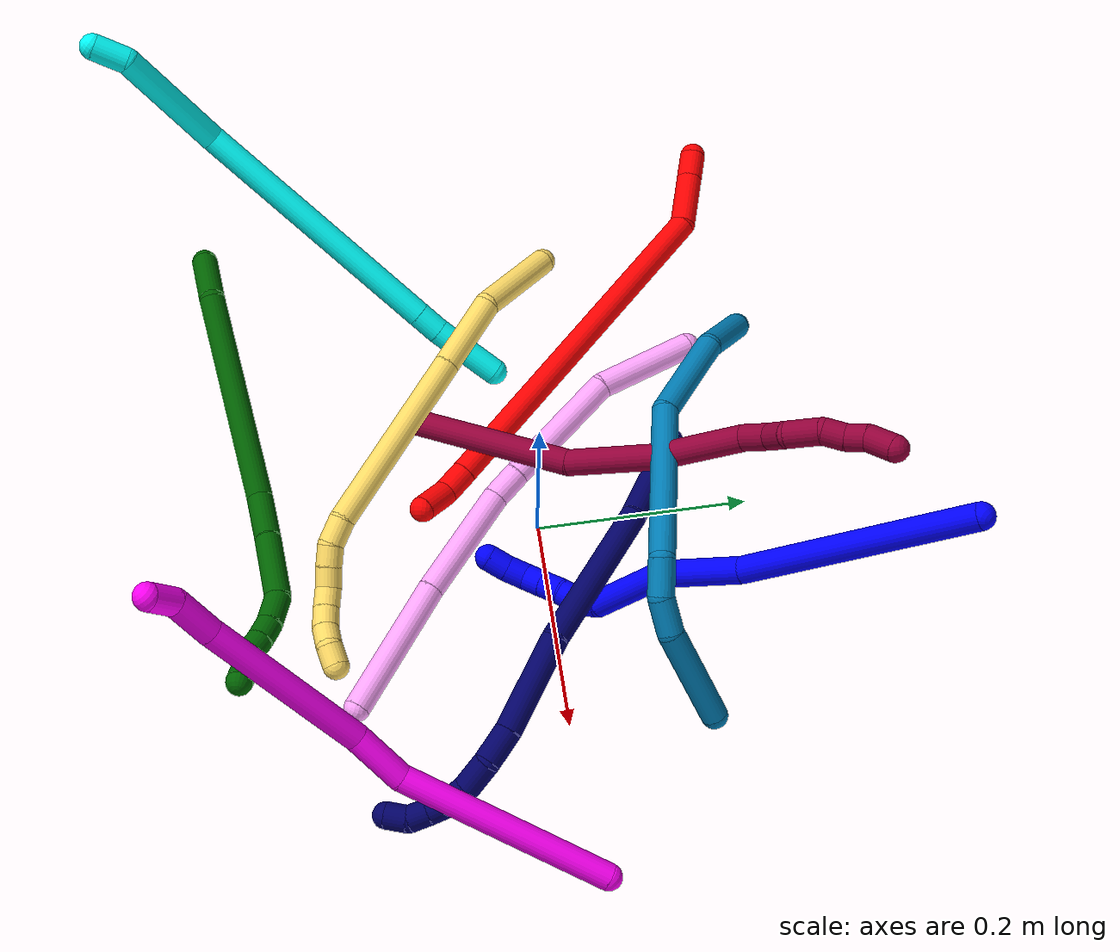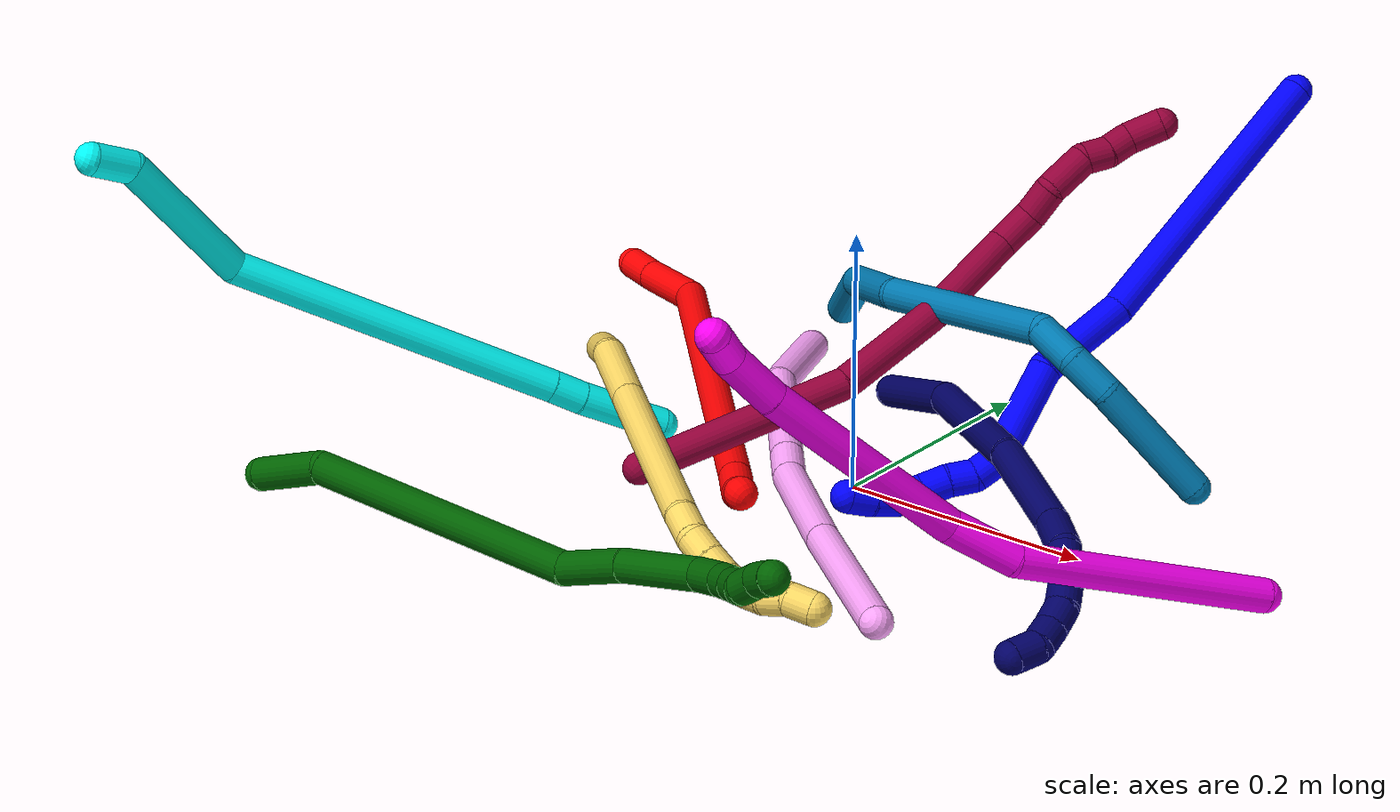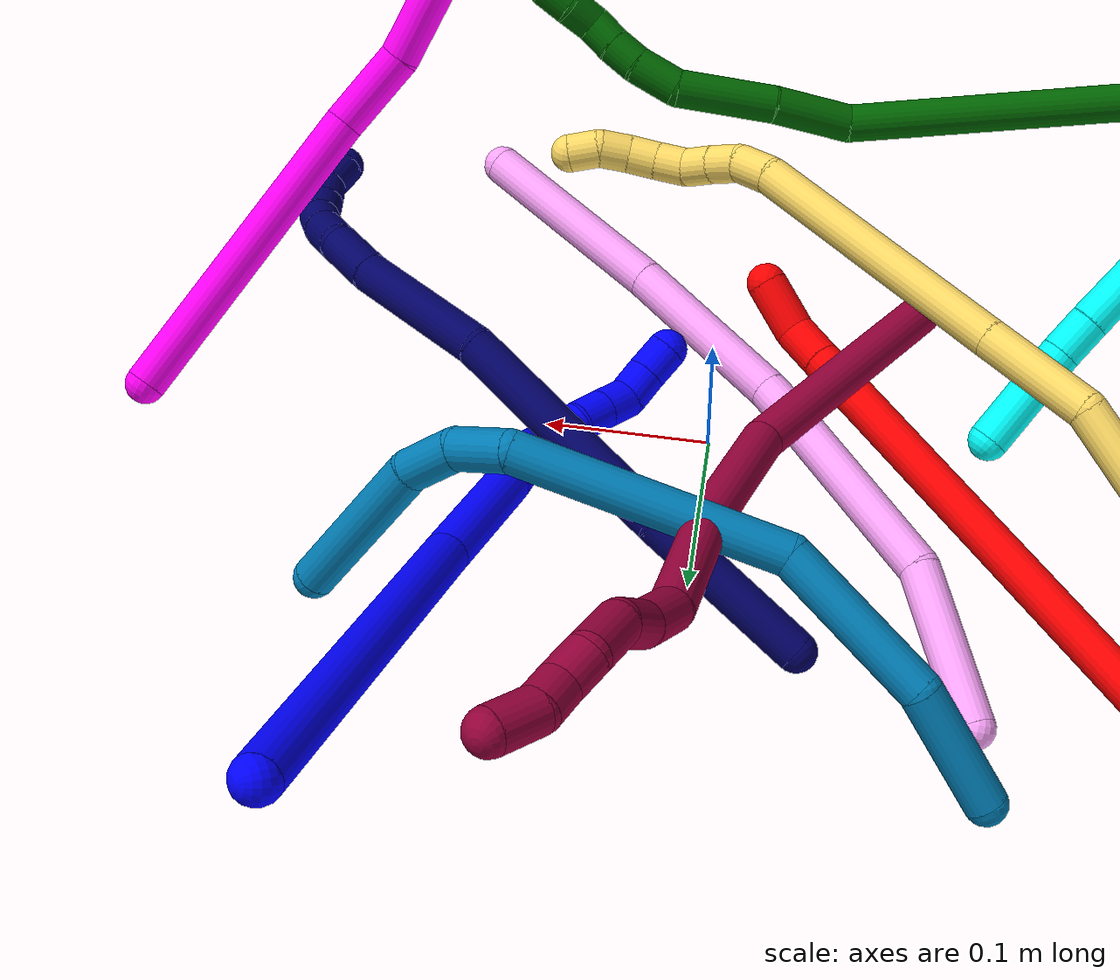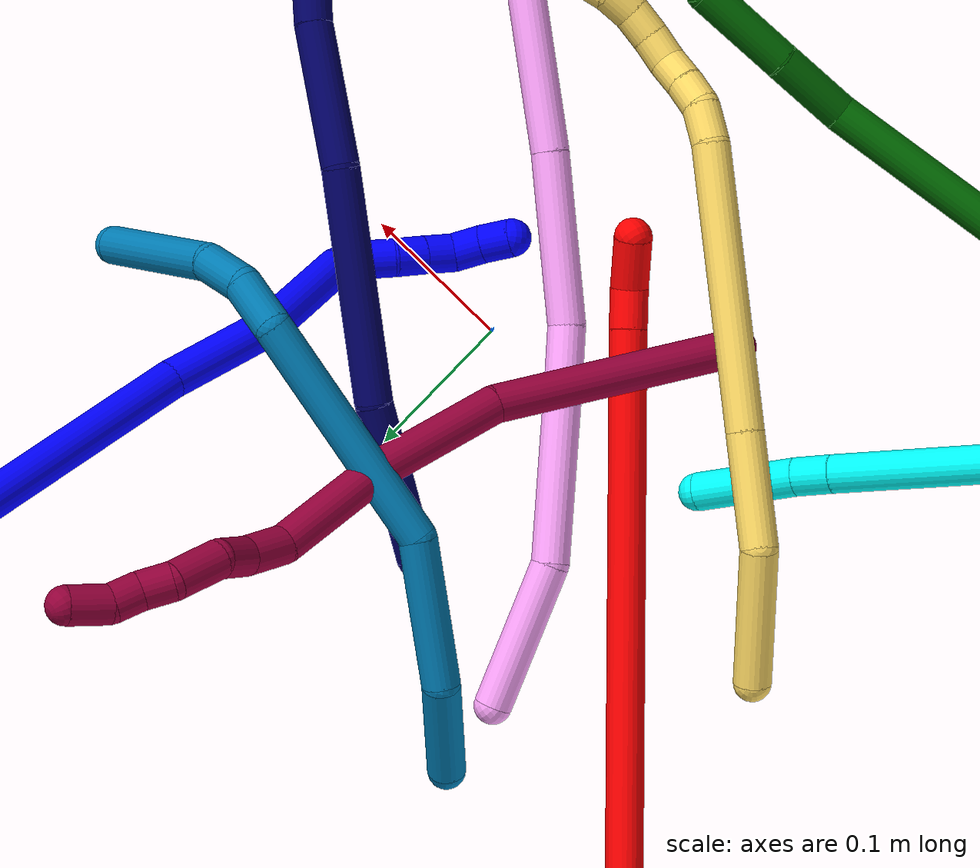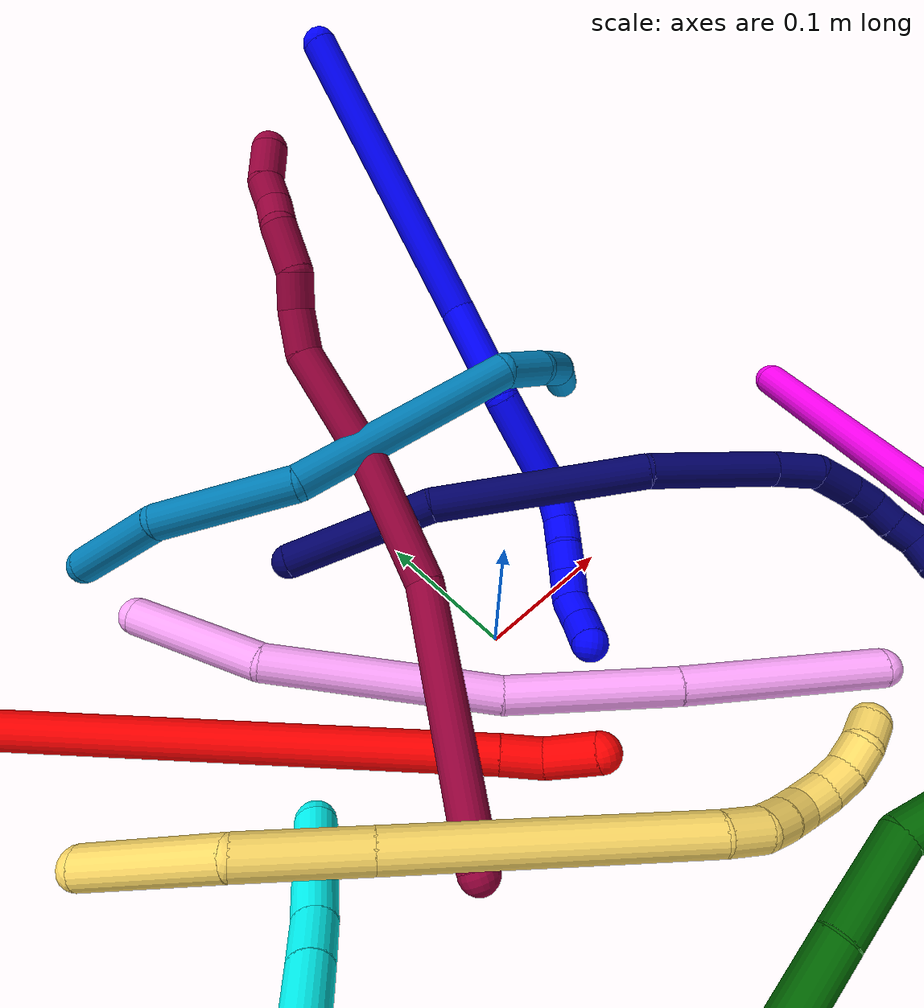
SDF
<sdf version="1.7">
 <world name="default">
  <plugin name="TubeGeneratorPlugin" filename="libtube_generator_plugin.so"/>
  <model name="photoneo_s_sensor">
   <static>1</static>
   <pose>0 0 2 1.57079 1.57079 3.14159</pose>
   <link name="link">
    <inertial><mass>0.1</mass></inertial>
    <sensor name="sensor" type="depth">
     <update_rate>30</update_rate>
     <camera>
      <horizontal_fov>1.22</horizontal_fov>
      <image><width>1920</width><height>1200</height><format>B8G8R8</format></image>
      <clip><near>0.1</near><far>2</far></clip>
      <depth_camera><output>points</output></depth_camera>
     </camera>
     <plugin name="camera_plugin" filename="libgazebo_ros_depth_camera.so">
      <baseline>0.2</baseline>
      <alwaysOn>1</alwaysOn>
      <updateRate>0.0</updateRate>
      <cameraName>camera_ir</cameraName>
      <imageTopicName>/camera/color/image_raw</imageTopicName>
      <cameraInfoTopicName>/camera/color/camera_info</cameraInfoTopicName>
      <depthImageTopicName>/camera/depth/image_raw</depthImageTopicName>
      <depthImageCameraInfoTopicName>/camera/depth/camera_info</depthImageCameraInfoTopicName>
      <pointCloudTopicName>/camera/depth/points</pointCloudTopicName>
      <frameName>fr_optical</frameName>
      <pointCloudCutoff>0.1</pointCloudCutoff>
      <pointCloudCutoffMax>2.0</pointCloudCutoffMax>
      <distortionK1>0</distortionK1>
      <distortionK2>0</distortionK2>
      <distortionK3>0</distortionK3>
      <distortionT1>0</distortionT1>
      <distortionT2>0</distortionT2>
      <CxPrime>0</CxPrime>
      <Cx>0</Cx>
      <Cy>0</Cy>
      <focalLength>0</focalLength>
      <hackBaseline>0</hackBaseline>
     </plugin>
    </sensor>
   </link>
  </model>
  <gravity>0 0 -9.8</gravity>
  <magnetic_field>6e-06 2.3e-05 -4.2e-05</magnetic_field>
  <atmosphere type="adiabatic"/>
  <physics name="default_physics" default="0" type="ode">
   <max_step_size>0.003</max_step_size>
   <real_time_factor>1</real_time_factor>
   <real_time_update_rate>1000</real_time_update_rate>
   <max_contacts>10000</max_contacts>
   <ode>
    <solver>
     <type>quick</type>
     <iters>100</iters>
     <sor>1.3</sor>
     <use_dynamic_moi_rescaling>0</use_dynamic_moi_rescaling>
    </solver>
    <constraints>
     <contact_max_correcting_vel>0</contact_max_correcting_vel>
     <contact_surface_layer>0.001</contact_surface_layer>
     <cfm>0</cfm>
     <erp>0.2</erp>
    </constraints>
   </ode>
  </physics>
  <scene><ambient>0.4 0.4 0.4 1</ambient><background>0.7 0.7 0.7 1</background><shadows>0</shadows></scene>
  <audio><device>default</device></audio>
  <spherical_coordinates>
   <surface_model>EARTH_WGS84</surface_model>
   <latitude_deg>0</latitude_deg>
   <longitude_deg>0</longitude_deg>
   <elevation>0</elevation>
   <heading_deg>0</heading_deg>
  </spherical_coordinates>
  <model name="bin">
   <static>1</static>
   <link name="bottom">
    <collision name="collision-bottom">
     <pose>0 0 -0.01 0 -0 0</pose>
     <geometry><box><size>0.8 0.6 0.02</size></box></geometry>
     <surface>
      <friction><ode><mu>100</mu><mu2>100</mu2></ode></friction>
      <contact><collide_bitmask>65535</collide_bitmask></contact>
     </surface>
    </collision>
   </link>
   <link name="west_wall">
    <collision name="collision-west_wall">
     <pose>-0.41 0 0.1 0 -0 0</pose>
     <geometry><box><size>0.02 0.6 0.2</size></box></geometry>
     <surface>
      <friction><ode><mu>100</mu><mu2>100</mu2></ode></friction>
      <contact><collide_bitmask>65535</collide_bitmask></contact>
     </surface>
    </collision>
   </link>
   <link name="east_wall">
    <collision name="collision-east_wall">
     <pose>0.41 0 0.1 0 -0 0</pose>
     <geometry><box><size>0.02 0.6 0.2</size></box></geometry>
     <surface>
      <friction><ode><mu>100</mu><mu2>100</mu2></ode></friction>
      <contact><collide_bitmask>65535</collide_bitmask></contact>
     </surface>
    </collision>
   </link>
   <link name="south_wall">
    <collision name="collision-south_wall">
     <pose>0 -0.31 0.1 0 -0 0</pose>
     <geometry><box><size>0.8 0.02 0.2</size></box></geometry>
     <surface>
      <friction><ode><mu>100</mu><mu2>100</mu2></ode></friction>
      <contact><collide_bitmask>65535</collide_bitmask></contact>
     </surface>
    </collision>
   </link>
   <link name="north_wall">
    <collision name="collision-north_wall">
     <pose>0 0.31 0.1 0 -0 0</pose>
     <geometry><box><size>0.8 0.02 0.2</size></box></geometry>
     <surface>
      <friction><ode><mu>100</mu><mu2>100</mu2></ode></friction>
      <contact><collide_bitmask>65535</collide_bitmask></contact>
     </surface>
    </collision>
   </link>
  </model>
  <model name="1">
   <static>0</static>
   <link name="1">
    <collision name="collision-cylinder-e_1_1_4">
     <pose>-0.001799 -0.067383 -0.090909 2.50374 -0.015895 -0.048129</pose>
     <geometry><cylinder><radius>0.0125</radius><length>0.226345</length></cylinder></geometry>
     <surface>
      <friction><ode><mu>1.16</mu><mu2>1.16</mu2><slip1>0</slip1><slip2>0</slip2></ode></friction>
      <contact><ode><kp>1e+06</kp><kd>1</kd><max_vel>0</max_vel><min_depth>0.001</min_depth></ode></contact>
     </surface>
    </collision>
    <visual name="visual-cylinder-e_1_1_4">
     <pose>-0.001799 -0.067383 -0.090909 2.50374 -0.015895 -0.048129</pose>
     <geometry><cylinder><radius>0.0125</radius><length>0.226345</length></cylinder></geometry>
     <material><ambient>0 0 1 1</ambient></material>
    </visual>
    <collision name="collision-cylinder-e_2_4_5">
     <pose>-0.010561 -0.153899 -0.213085 2.59247 -0.187722 -0.645073</pose>
     <geometry><cylinder><radius>0.0125</radius><length>0.074626</length></cylinder></geometry>
     <surface>
      <friction><ode><mu>1.16</mu><mu2>1.16</mu2><slip1>0</slip1><slip2>0</slip2></ode></friction>
      <contact><ode><kp>1e+06</kp><kd>1</kd><max_vel>0</max_vel><min_depth>0.001</min_depth></ode></contact>
     </surface>
    </collision>
    <visual name="visual-cylinder-e_2_4_5">
     <pose>-0.010561 -0.153899 -0.213085 2.59247 -0.187722 -0.645073</pose>
     <geometry><cylinder><radius>0.0125</radius><length>0.074626</length></cylinder></geometry>
     <material><ambient>0 0 1 1</ambient></material>
    </visual>
    <collision name="collision-cylinder-e_3_5_6">
     <pose>-0.011324 -0.199096 -0.273027 2.40383 0.158678 0.405674</pose>
     <geometry><cylinder><radius>0.0125</radius><length>0.078484</length></cylinder></geometry>
     <surface>
      <friction><ode><mu>1.16</mu><mu2>1.16</mu2><slip1>0</slip1><slip2>0</slip2></ode></friction>
      <contact><ode><kp>1e+06</kp><kd>1</kd><max_vel>0</max_vel><min_depth>0.001</min_depth></ode></contact>
     </surface>
    </collision>
    <visual name="visual-cylinder-e_3_5_6">
     <pose>-0.011324 -0.199096 -0.273027 2.40383 0.158678 0.405674</pose>
     <geometry><cylinder><radius>0.0125</radius><length>0.078484</length></cylinder></geometry>
     <material><ambient>0 0 1 1</ambient></material>
    </visual>
    <collision name="collision-cylinder-e_4_6_7">
     <pose>-0.006063 -0.228559 -0.311192 2.7977 -0.092996 -0.523595</pose>
     <geometry><cylinder><radius>0.0125</radius><length>0.020253</length></cylinder></geometry>
     <surface>
      <friction><ode><mu>1.16</mu><mu2>1.16</mu2><slip1>0</slip1><slip2>0</slip2></ode></friction>
      <contact><ode><kp>1e+06</kp><kd>1</kd><max_vel>0</max_vel><min_depth>0.001</min_depth></ode></contact>
     </surface>
    </collision>
    <visual name="visual-cylinder-e_4_6_7">
     <pose>-0.006063 -0.228559 -0.311192 2.7977 -0.092996 -0.523595</pose>
     <geometry><cylinder><radius>0.0125</radius><length>0.020253</length></cylinder></geometry>
     <material><ambient>0 0 1 1</ambient></material>
    </visual>
    <collision name="collision-cylinder-e_5_7_8">
     <pose>-0.01125 -0.23255 -0.329769 3.0766 -0.436398 -2.85044</pose>
     <geometry><cylinder><radius>0.0125</radius><length>0.020091</length></cylinder></geometry>
     <surface>
      <friction><ode><mu>1.16</mu><mu2>1.16</mu2><slip1>0</slip1><slip2>0</slip2></ode></friction>
      <contact><ode><kp>1e+06</kp><kd>1</kd><max_vel>0</max_vel><min_depth>0.001</min_depth></ode></contact>
     </surface>
    </collision>
    <visual name="visual-cylinder-e_5_7_8">
     <pose>-0.01125 -0.23255 -0.329769 3.0766 -0.436398 -2.85044</pose>
     <geometry><cylinder><radius>0.0125</radius><length>0.020091</length></cylinder></geometry>
     <material><ambient>0 0 1 1</ambient></material>
    </visual>
    <collision name="collision-cylinder-e_6_8_9">
     <pose>-0.018055 -0.234586 -0.348425 2.99176 -0.258481 -2.09412</pose>
     <geometry><cylinder><radius>0.0125</radius><length>0.020024</length></cylinder></geometry>
     <surface>
      <friction><ode><mu>1.16</mu><mu2>1.16</mu2><slip1>0</slip1><slip2>0</slip2></ode></friction>
      <contact><ode><kp>1e+06</kp><kd>1</kd><max_vel>0</max_vel><min_depth>0.001</min_depth></ode></contact>
     </surface>
    </collision>
    <visual name="visual-cylinder-e_6_8_9">
     <pose>-0.018055 -0.234586 -0.348425 2.99176 -0.258481 -2.09412</pose>
     <geometry><cylinder><radius>0.0125</radius><length>0.020024</length></cylinder></geometry>
     <material><ambient>0 0 1 1</ambient></material>
    </visual>
    <collision name="collision-cylinder-e_7_9_10">
     <pose>-0.023195 -0.237292 -0.367659 3.01177 -0.258878 -2.21531</pose>
     <geometry><cylinder><radius>0.0125</radius><length>0.020161</length></cylinder></geometry>
     <surface>
      <friction><ode><mu>1.16</mu><mu2>1.16</mu2><slip1>0</slip1><slip2>0</slip2></ode></friction>
      <contact><ode><kp>1e+06</kp><kd>1</kd><max_vel>0</max_vel><min_depth>0.001</min_depth></ode></contact>
     </surface>
    </collision>
    <visual name="visual-cylinder-e_7_9_10">
     <pose>-0.023195 -0.237292 -0.367659 3.01177 -0.258878 -2.21531</pose>
     <geometry><cylinder><radius>0.0125</radius><length>0.020161</length></cylinder></geometry>
     <material><ambient>0 0 1 1</ambient></material>
    </visual>
    <collision name="collision-cylinder-e_8_10_11">
     <pose>-0.032705 -0.240187 -0.384351 2.91322 -0.765172 -2.58632</pose>
     <geometry><cylinder><radius>0.0125</radius><length>0.020009</length></cylinder></geometry>
     <surface>
      <friction><ode><mu>1.16</mu><mu2>1.16</mu2><slip1>0</slip1><slip2>0</slip2></ode></friction>
      <contact><ode><kp>1e+06</kp><kd>1</kd><max_vel>0</max_vel><min_depth>0.001</min_depth></ode></contact>
     </surface>
    </collision>
    <visual name="visual-cylinder-e_8_10_11">
     <pose>-0.032705 -0.240187 -0.384351 2.91322 -0.765172 -2.58632</pose>
     <geometry><cylinder><radius>0.0125</radius><length>0.020009</length></cylinder></geometry>
     <material><ambient>0 0 1 1</ambient></material>
    </visual>
    <collision name="collision-cylinder-e_9_11_2">
     <pose>-0.047157 -0.242345 -0.397952 3.06202 -0.851044 -2.96637</pose>
     <geometry><cylinder><radius>0.0125</radius><length>0.020006</length></cylinder></geometry>
     <surface>
      <friction><ode><mu>1.16</mu><mu2>1.16</mu2><slip1>0</slip1><slip2>0</slip2></ode></friction>
      <contact><ode><kp>1e+06</kp><kd>1</kd><max_vel>0</max_vel><min_depth>0.001</min_depth></ode></contact>
     </surface>
    </collision>
    <visual name="visual-cylinder-e_9_11_2">
     <pose>-0.047157 -0.242345 -0.397952 3.06202 -0.851044 -2.96637</pose>
     <geometry><cylinder><radius>0.0125</radius><length>0.020006</length></cylinder></geometry>
     <material><ambient>0 0 1 1</ambient></material>
    </visual>
    <collision name="collision-sphere-2">
     <pose>-0.054679 -0.242869 -0.404525 0 -0 0</pose>
     <geometry><sphere><radius>0.0125</radius></sphere></geometry>
     <surface>
      <friction><ode><mu>1.16</mu><mu2>1.16</mu2><slip1>0</slip1><slip2>0</slip2></ode></friction>
      <contact><ode><kp>1e+06</kp><kd>1</kd><max_vel>0</max_vel><min_depth>0.001</min_depth></ode></contact>
     </surface>
    </collision>
    <visual name="visual-sphere-2">
     <pose>-0.054679 -0.242869 -0.404525 0 -0 0</pose>
     <geometry><sphere><radius>0.0125</radius></sphere></geometry>
     <material><ambient>0 0 1 1</ambient></material>
    </visual>
    <collision name="collision-sphere-11">
     <pose>-0.039635 -0.241821 -0.391379 0 -0 0</pose>
     <geometry><sphere><radius>0.0125</radius></sphere></geometry>
     <surface>
      <friction><ode><mu>1.16</mu><mu2>1.16</mu2><slip1>0</slip1><slip2>0</slip2></ode></friction>
      <contact><ode><kp>1e+06</kp><kd>1</kd><max_vel>0</max_vel><min_depth>0.001</min_depth></ode></contact>
     </surface>
    </collision>
    <visual name="visual-sphere-11">
     <pose>-0.039635 -0.241821 -0.391379 0 -0 0</pose>
     <geometry><sphere><radius>0.0125</radius></sphere></geometry>
     <material><ambient>0 0 1 1</ambient></material>
    </visual>
    <collision name="collision-sphere-10">
     <pose>-0.025775 -0.238554 -0.377322 0 -0 0</pose>
     <geometry><sphere><radius>0.0125</radius></sphere></geometry>
     <surface>
      <friction><ode><mu>1.16</mu><mu2>1.16</mu2><slip1>0</slip1><slip2>0</slip2></ode></friction>
      <contact><ode><kp>1e+06</kp><kd>1</kd><max_vel>0</max_vel><min_depth>0.001</min_depth></ode></contact>
     </surface>
    </collision>
    <visual name="visual-sphere-10">
     <pose>-0.025775 -0.238554 -0.377322 0 -0 0</pose>
     <geometry><sphere><radius>0.0125</radius></sphere></geometry>
     <material><ambient>0 0 1 1</ambient></material>
    </visual>
    <collision name="collision-sphere-9">
     <pose>-0.020614 -0.236031 -0.357996 0 -0 0</pose>
     <geometry><sphere><radius>0.0125</radius></sphere></geometry>
     <surface>
      <friction><ode><mu>1.16</mu><mu2>1.16</mu2><slip1>0</slip1><slip2>0</slip2></ode></friction>
      <contact><ode><kp>1e+06</kp><kd>1</kd><max_vel>0</max_vel><min_depth>0.001</min_depth></ode></contact>
     </surface>
    </collision>
    <visual name="visual-sphere-9">
     <pose>-0.020614 -0.236031 -0.357996 0 -0 0</pose>
     <geometry><sphere><radius>0.0125</radius></sphere></geometry>
     <material><ambient>0 0 1 1</ambient></material>
    </visual>
    <collision name="collision-sphere-4">
     <pose>-0.003598 -0.134766 -0.181817 0 -0 0</pose>
     <geometry><sphere><radius>0.0125</radius></sphere></geometry>
     <surface>
      <friction><ode><mu>1.16</mu><mu2>1.16</mu2><slip1>0</slip1><slip2>0</slip2></ode></friction>
      <contact><ode><kp>1e+06</kp><kd>1</kd><max_vel>0</max_vel><min_depth>0.001</min_depth></ode></contact>
     </surface>
    </collision>
    <visual name="visual-sphere-4">
     <pose>-0.003598 -0.134766 -0.181817 0 -0 0</pose>
     <geometry><sphere><radius>0.0125</radius></sphere></geometry>
     <material><ambient>0 0 1 1</ambient></material>
    </visual>
    <collision name="collision-sphere-1">
     <geometry><sphere><radius>0.0125</radius></sphere></geometry>
     <surface>
      <friction><ode><mu>1.16</mu><mu2>1.16</mu2><slip1>0</slip1><slip2>0</slip2></ode></friction>
      <contact><ode><kp>1e+06</kp><kd>1</kd><max_vel>0</max_vel><min_depth>0.001</min_depth></ode></contact>
     </surface>
    </collision>
    <visual name="visual-sphere-1">
     <geometry><sphere><radius>0.0125</radius></sphere></geometry>
     <material><ambient>0 0 1 1</ambient></material>
    </visual>
    <collision name="collision-sphere-8">
     <pose>-0.015496 -0.233141 -0.338854 0 -0 0</pose>
     <geometry><sphere><radius>0.0125</radius></sphere></geometry>
     <surface>
      <friction><ode><mu>1.16</mu><mu2>1.16</mu2><slip1>0</slip1><slip2>0</slip2></ode></friction>
      <contact><ode><kp>1e+06</kp><kd>1</kd><max_vel>0</max_vel><min_depth>0.001</min_depth></ode></contact>
     </surface>
    </collision>
    <visual name="visual-sphere-8">
     <pose>-0.015496 -0.233141 -0.338854 0 -0 0</pose>
     <geometry><sphere><radius>0.0125</radius></sphere></geometry>
     <material><ambient>0 0 1 1</ambient></material>
    </visual>
    <collision name="collision-sphere-5">
     <pose>-0.017524 -0.173032 -0.244354 0 -0 0</pose>
     <geometry><sphere><radius>0.0125</radius></sphere></geometry>
     <surface>
      <friction><ode><mu>1.16</mu><mu2>1.16</mu2><slip1>0</slip1><slip2>0</slip2></ode></friction>
      <contact><ode><kp>1e+06</kp><kd>1</kd><max_vel>0</max_vel><min_depth>0.001</min_depth></ode></contact>
     </surface>
    </collision>
    <visual name="visual-sphere-5">
     <pose>-0.017524 -0.173032 -0.244354 0 -0 0</pose>
     <geometry><sphere><radius>0.0125</radius></sphere></geometry>
     <material><ambient>0 0 1 1</ambient></material>
    </visual>
    <collision name="collision-sphere-6">
     <pose>-0.005123 -0.225159 -0.3017 0 -0 0</pose>
     <geometry><sphere><radius>0.0125</radius></sphere></geometry>
     <surface>
      <friction><ode><mu>1.16</mu><mu2>1.16</mu2><slip1>0</slip1><slip2>0</slip2></ode></friction>
      <contact><ode><kp>1e+06</kp><kd>1</kd><max_vel>0</max_vel><min_depth>0.001</min_depth></ode></contact>
     </surface>
    </collision>
    <visual name="visual-sphere-6">
     <pose>-0.005123 -0.225159 -0.3017 0 -0 0</pose>
     <geometry><sphere><radius>0.0125</radius></sphere></geometry>
     <material><ambient>0 0 1 1</ambient></material>
    </visual>
    <collision name="collision-sphere-7">
     <pose>-0.007004 -0.231958 -0.320685 0 -0 0</pose>
     <geometry><sphere><radius>0.0125</radius></sphere></geometry>
     <surface>
      <friction><ode><mu>1.16</mu><mu2>1.16</mu2><slip1>0</slip1><slip2>0</slip2></ode></friction>
      <contact><ode><kp>1e+06</kp><kd>1</kd><max_vel>0</max_vel><min_depth>0.001</min_depth></ode></contact>
     </surface>
    </collision>
    <visual name="visual-sphere-7">
     <pose>-0.007004 -0.231958 -0.320685 0 -0 0</pose>
     <geometry><sphere><radius>0.0125</radius></sphere></geometry>
     <material><ambient>0 0 1 1</ambient></material>
    </visual>
    <inertial>
     <pose>-0.00972 -0.141599 -0.201752 0 -0 0</pose>
     <mass>0.5</mass>
     <inertia>
      <ixx>0.000979</ixx>
      <ixy>0</ixy>
      <ixz>0</ixz>
      <iyy>-0.000904</iyy>
      <iyz>0</iyz>
      <izz>0.000618</izz>
     </inertia>
    </inertial>
   </link>
   <pose>0.153022 0.348188 0.246939 0.542533 0.958439 1.28035</pose>
  </model>
  <model name="2">
   <static>0</static>
   <link name="2">
    <collision name="collision-cylinder-e_1_1_4">
     <pose>0.003169 0.000118 -0.013701 -3.133 0.227264 -3.06637</pose>
     <geometry><cylinder><radius>0.0125</radius><length>0.028126</length></cylinder></geometry>
     <surface>
      <friction><ode><mu>1.16</mu><mu2>1.16</mu2><slip1>0</slip1><slip2>0</slip2></ode></friction>
      <contact><ode><kp>1e+06</kp><kd>1</kd><max_vel>0</max_vel><min_depth>0.001</min_depth></ode></contact>
     </surface>
    </collision>
    <visual name="visual-cylinder-e_1_1_4">
     <pose>0.003169 0.000118 -0.013701 -3.133 0.227264 -3.06637</pose>
     <geometry><cylinder><radius>0.0125</radius><length>0.028126</length></cylinder></geometry>
     <material><ambient>1 0 0 1</ambient></material>
    </visual>
    <collision name="collision-cylinder-e_2_4_5">
     <pose>0.014129 0.001099 -0.053923 -3.10905 0.285614 -2.91617</pose>
     <geometry><cylinder><radius>0.0125</radius><length>0.055311</length></cylinder></geometry>
     <surface>
      <friction><ode><mu>1.16</mu><mu2>1.16</mu2><slip1>0</slip1><slip2>0</slip2></ode></friction>
      <contact><ode><kp>1e+06</kp><kd>1</kd><max_vel>0</max_vel><min_depth>0.001</min_depth></ode></contact>
     </surface>
    </collision>
    <visual name="visual-cylinder-e_2_4_5">
     <pose>0.014129 0.001099 -0.053923 -3.10905 0.285614 -2.91617</pose>
     <geometry><cylinder><radius>0.0125</radius><length>0.055311</length></cylinder></geometry>
     <material><ambient>1 0 0 1</ambient></material>
    </visual>
    <collision name="collision-cylinder-e_3_5_6">
     <pose>0.091714 -0.075022 -0.223837 2.64888 0.405112 1.36969</pose>
     <geometry><cylinder><radius>0.0125</radius><length>0.35417</length></cylinder></geometry>
     <surface>
      <friction><ode><mu>1.16</mu><mu2>1.16</mu2><slip1>0</slip1><slip2>0</slip2></ode></friction>
      <contact><ode><kp>1e+06</kp><kd>1</kd><max_vel>0</max_vel><min_depth>0.001</min_depth></ode></contact>
     </surface>
    </collision>
    <visual name="visual-cylinder-e_3_5_6">
     <pose>0.091714 -0.075022 -0.223837 2.64888 0.405112 1.36969</pose>
     <geometry><cylinder><radius>0.0125</radius><length>0.35417</length></cylinder></geometry>
     <material><ambient>1 0 0 1</ambient></material>
    </visual>
    <collision name="collision-cylinder-e_4_6_7">
     <pose>0.16664 -0.158325 -0.378242 2.62062 0.384217 1.26081</pose>
     <geometry><cylinder><radius>0.0125</radius><length>0.027388</length></cylinder></geometry>
     <surface>
      <friction><ode><mu>1.16</mu><mu2>1.16</mu2><slip1>0</slip1><slip2>0</slip2></ode></friction>
      <contact><ode><kp>1e+06</kp><kd>1</kd><max_vel>0</max_vel><min_depth>0.001</min_depth></ode></contact>
     </surface>
    </collision>
    <visual name="visual-cylinder-e_4_6_7">
     <pose>0.16664 -0.158325 -0.378242 2.62062 0.384217 1.26081</pose>
     <geometry><cylinder><radius>0.0125</radius><length>0.027388</length></cylinder></geometry>
     <material><ambient>1 0 0 1</ambient></material>
    </visual>
    <collision name="collision-cylinder-e_5_7_2">
     <pose>0.184693 -0.169952 -0.399799 2.67531 0.830397 2.15339</pose>
     <geometry><cylinder><radius>0.0125</radius><length>0.035004</length></cylinder></geometry>
     <surface>
      <friction><ode><mu>1.16</mu><mu2>1.16</mu2><slip1>0</slip1><slip2>0</slip2></ode></friction>
      <contact><ode><kp>1e+06</kp><kd>1</kd><max_vel>0</max_vel><min_depth>0.001</min_depth></ode></contact>
     </surface>
    </collision>
    <visual name="visual-cylinder-e_5_7_2">
     <pose>0.184693 -0.169952 -0.399799 2.67531 0.830397 2.15339</pose>
     <geometry><cylinder><radius>0.0125</radius><length>0.035004</length></cylinder></geometry>
     <material><ambient>1 0 0 1</ambient></material>
    </visual>
    <collision name="collision-sphere-2">
     <pose>0.197613 -0.17526 -0.410345 0 -0 0</pose>
     <geometry><sphere><radius>0.0125</radius></sphere></geometry>
     <surface>
      <friction><ode><mu>1.16</mu><mu2>1.16</mu2><slip1>0</slip1><slip2>0</slip2></ode></friction>
      <contact><ode><kp>1e+06</kp><kd>1</kd><max_vel>0</max_vel><min_depth>0.001</min_depth></ode></contact>
     </surface>
    </collision>
    <visual name="visual-sphere-2">
     <pose>0.197613 -0.17526 -0.410345 0 -0 0</pose>
     <geometry><sphere><radius>0.0125</radius></sphere></geometry>
     <material><ambient>1 0 0 1</ambient></material>
    </visual>
    <collision name="collision-sphere-7">
     <pose>0.171773 -0.164644 -0.389253 0 -0 0</pose>
     <geometry><sphere><radius>0.0125</radius></sphere></geometry>
     <surface>
      <friction><ode><mu>1.16</mu><mu2>1.16</mu2><slip1>0</slip1><slip2>0</slip2></ode></friction>
      <contact><ode><kp>1e+06</kp><kd>1</kd><max_vel>0</max_vel><min_depth>0.001</min_depth></ode></contact>
     </surface>
    </collision>
    <visual name="visual-sphere-7">
     <pose>0.171773 -0.164644 -0.389253 0 -0 0</pose>
     <geometry><sphere><radius>0.0125</radius></sphere></geometry>
     <material><ambient>1 0 0 1</ambient></material>
    </visual>
    <collision name="collision-sphere-6">
     <pose>0.161507 -0.152006 -0.36723 0 -0 0</pose>
     <geometry><sphere><radius>0.0125</radius></sphere></geometry>
     <surface>
      <friction><ode><mu>1.16</mu><mu2>1.16</mu2><slip1>0</slip1><slip2>0</slip2></ode></friction>
      <contact><ode><kp>1e+06</kp><kd>1</kd><max_vel>0</max_vel><min_depth>0.001</min_depth></ode></contact>
     </surface>
    </collision>
    <visual name="visual-sphere-6">
     <pose>0.161507 -0.152006 -0.36723 0 -0 0</pose>
     <geometry><sphere><radius>0.0125</radius></sphere></geometry>
     <material><ambient>1 0 0 1</ambient></material>
    </visual>
    <collision name="collision-sphere-5">
     <pose>0.021921 0.001962 -0.080444 0 -0 0</pose>
     <geometry><sphere><radius>0.0125</radius></sphere></geometry>
     <surface>
      <friction><ode><mu>1.16</mu><mu2>1.16</mu2><slip1>0</slip1><slip2>0</slip2></ode></friction>
      <contact><ode><kp>1e+06</kp><kd>1</kd><max_vel>0</max_vel><min_depth>0.001</min_depth></ode></contact>
     </surface>
    </collision>
    <visual name="visual-sphere-5">
     <pose>0.021921 0.001962 -0.080444 0 -0 0</pose>
     <geometry><sphere><radius>0.0125</radius></sphere></geometry>
     <material><ambient>1 0 0 1</ambient></material>
    </visual>
    <collision name="collision-sphere-1">
     <geometry><sphere><radius>0.0125</radius></sphere></geometry>
     <surface>
      <friction><ode><mu>1.16</mu><mu2>1.16</mu2><slip1>0</slip1><slip2>0</slip2></ode></friction>
      <contact><ode><kp>1e+06</kp><kd>1</kd><max_vel>0</max_vel><min_depth>0.001</min_depth></ode></contact>
     </surface>
    </collision>
    <visual name="visual-sphere-1">
     <geometry><sphere><radius>0.0125</radius></sphere></geometry>
     <material><ambient>1 0 0 1</ambient></material>
    </visual>
    <collision name="collision-sphere-4">
     <pose>0.006337 0.000235 -0.027402 0 -0 0</pose>
     <geometry><sphere><radius>0.0125</radius></sphere></geometry>
     <surface>
      <friction><ode><mu>1.16</mu><mu2>1.16</mu2><slip1>0</slip1><slip2>0</slip2></ode></friction>
      <contact><ode><kp>1e+06</kp><kd>1</kd><max_vel>0</max_vel><min_depth>0.001</min_depth></ode></contact>
     </surface>
    </collision>
    <visual name="visual-sphere-4">
     <pose>0.006337 0.000235 -0.027402 0 -0 0</pose>
     <geometry><sphere><radius>0.0125</radius></sphere></geometry>
     <material><ambient>1 0 0 1</ambient></material>
    </visual>
    <inertial>
     <pose>0.088764 -0.073583 -0.213997 0 -0 0</pose>
     <mass>0.5</mass>
     <inertia>
      <ixx>0.004026</ixx>
      <ixy>0</ixy>
      <ixz>0</ixz>
      <iyy>0.003381</iyy>
      <iyz>0</iyz>
      <izz>0.000111</izz>
     </inertia>
    </inertial>
   </link>
   <pose>-0.387417 0.21808 0.014003 0.853855 -1.14232 -1.13602</pose>
  </model>
  <model name="3">
   <static>0</static>
   <link name="3">
    <collision name="collision-cylinder-e_1_1_4">
     <pose>-5e-06 -0.000323 0.034046 0.009489 -0.000144 -1e-06</pose>
     <geometry><cylinder><radius>0.0125</radius><length>0.068096</length></cylinder></geometry>
     <surface>
      <friction><ode><mu>1.16</mu><mu2>1.16</mu2><slip1>0</slip1><slip2>0</slip2></ode></friction>
      <contact><ode><kp>1e+06</kp><kd>1</kd><max_vel>0</max_vel><min_depth>0.001</min_depth></ode></contact>
     </surface>
    </collision>
    <visual name="visual-cylinder-e_1_1_4">
     <pose>-5e-06 -0.000323 0.034046 0.009489 -0.000144 -1e-06</pose>
     <geometry><cylinder><radius>0.0125</radius><length>0.068096</length></cylinder></geometry>
     <material><ambient>0.003922 1 0.996078 1</ambient></material>
    </visual>
    <collision name="collision-cylinder-e_2_4_5">
     <pose>-0.000521 -0.00163 0.0807 0.07784 -0.04042 -0.001574</pose>
     <geometry><cylinder><radius>0.0125</radius><length>0.025311</length></cylinder></geometry>
     <surface>
      <friction><ode><mu>1.16</mu><mu2>1.16</mu2><slip1>0</slip1><slip2>0</slip2></ode></friction>
      <contact><ode><kp>1e+06</kp><kd>1</kd><max_vel>0</max_vel><min_depth>0.001</min_depth></ode></contact>
     </surface>
    </collision>
    <visual name="visual-cylinder-e_2_4_5">
     <pose>-0.000521 -0.00163 0.0807 0.07784 -0.04042 -0.001574</pose>
     <geometry><cylinder><radius>0.0125</radius><length>0.025311</length></cylinder></geometry>
     <material><ambient>0.003922 1 0.996078 1</ambient></material>
    </visual>
    <collision name="collision-cylinder-e_3_5_6">
     <pose>-0.002179 -0.01444 0.221956 0.091674 -0.008875 -0.000407</pose>
     <geometry><cylinder><radius>0.0125</radius><length>0.258393</length></cylinder></geometry>
     <surface>
      <friction><ode><mu>1.16</mu><mu2>1.16</mu2><slip1>0</slip1><slip2>0</slip2></ode></friction>
      <contact><ode><kp>1e+06</kp><kd>1</kd><max_vel>0</max_vel><min_depth>0.001</min_depth></ode></contact>
     </surface>
    </collision>
    <visual name="visual-cylinder-e_3_5_6">
     <pose>-0.002179 -0.01444 0.221956 0.091674 -0.008875 -0.000407</pose>
     <geometry><cylinder><radius>0.0125</radius><length>0.258393</length></cylinder></geometry>
     <material><ambient>0.003922 1 0.996078 1</ambient></material>
    </visual>
    <collision name="collision-cylinder-e_4_6_7">
     <pose>-0.028888 -0.023341 0.402153 -0.056702 -0.459716 0.013271</pose>
     <geometry><cylinder><radius>0.0125</radius><length>0.115225</length></cylinder></geometry>
     <surface>
      <friction><ode><mu>1.16</mu><mu2>1.16</mu2><slip1>0</slip1><slip2>0</slip2></ode></friction>
      <contact><ode><kp>1e+06</kp><kd>1</kd><max_vel>0</max_vel><min_depth>0.001</min_depth></ode></contact>
     </surface>
    </collision>
    <visual name="visual-cylinder-e_4_6_7">
     <pose>-0.028888 -0.023341 0.402153 -0.056702 -0.459716 0.013271</pose>
     <geometry><cylinder><radius>0.0125</radius><length>0.115225</length></cylinder></geometry>
     <material><ambient>0.003922 1 0.996078 1</ambient></material>
    </visual>
    <collision name="collision-cylinder-e_5_7_2">
     <pose>-0.054245 -0.016326 0.469672 -0.250641 0.012445 -0.001568</pose>
     <geometry><cylinder><radius>0.0125</radius><length>0.032974</length></cylinder></geometry>
     <surface>
      <friction><ode><mu>1.16</mu><mu2>1.16</mu2><slip1>0</slip1><slip2>0</slip2></ode></friction>
      <contact><ode><kp>1e+06</kp><kd>1</kd><max_vel>0</max_vel><min_depth>0.001</min_depth></ode></contact>
     </surface>
    </collision>
    <visual name="visual-cylinder-e_5_7_2">
     <pose>-0.054245 -0.016326 0.469672 -0.250641 0.012445 -0.001568</pose>
     <geometry><cylinder><radius>0.0125</radius><length>0.032974</length></cylinder></geometry>
     <material><ambient>0.003922 1 0.996078 1</ambient></material>
    </visual>
    <collision name="collision-sphere-2">
     <pose>-0.05404 -0.012237 0.485643 0 -0 0</pose>
     <geometry><sphere><radius>0.0125</radius></sphere></geometry>
     <surface>
      <friction><ode><mu>1.16</mu><mu2>1.16</mu2><slip1>0</slip1><slip2>0</slip2></ode></friction>
      <contact><ode><kp>1e+06</kp><kd>1</kd><max_vel>0</max_vel><min_depth>0.001</min_depth></ode></contact>
     </surface>
    </collision>
    <visual name="visual-sphere-2">
     <pose>-0.05404 -0.012237 0.485643 0 -0 0</pose>
     <geometry><sphere><radius>0.0125</radius></sphere></geometry>
     <material><ambient>0.003922 1 0.996078 1</ambient></material>
    </visual>
    <collision name="collision-sphere-7">
     <pose>-0.054451 -0.020415 0.453702 0 -0 0</pose>
     <geometry><sphere><radius>0.0125</radius></sphere></geometry>
     <surface>
      <friction><ode><mu>1.16</mu><mu2>1.16</mu2><slip1>0</slip1><slip2>0</slip2></ode></friction>
      <contact><ode><kp>1e+06</kp><kd>1</kd><max_vel>0</max_vel><min_depth>0.001</min_depth></ode></contact>
     </surface>
    </collision>
    <visual name="visual-sphere-7">
     <pose>-0.054451 -0.020415 0.453702 0 -0 0</pose>
     <geometry><sphere><radius>0.0125</radius></sphere></geometry>
     <material><ambient>0.003922 1 0.996078 1</ambient></material>
    </visual>
    <collision name="collision-sphere-6">
     <pose>-0.003326 -0.026267 0.350605 0 -0 0</pose>
     <geometry><sphere><radius>0.0125</radius></sphere></geometry>
     <surface>
      <friction><ode><mu>1.16</mu><mu2>1.16</mu2><slip1>0</slip1><slip2>0</slip2></ode></friction>
      <contact><ode><kp>1e+06</kp><kd>1</kd><max_vel>0</max_vel><min_depth>0.001</min_depth></ode></contact>
     </surface>
    </collision>
    <visual name="visual-sphere-6">
     <pose>-0.003326 -0.026267 0.350605 0 -0 0</pose>
     <geometry><sphere><radius>0.0125</radius></sphere></geometry>
     <material><ambient>0.003922 1 0.996078 1</ambient></material>
    </visual>
    <collision name="collision-sphere-5">
     <pose>-0.001033 -0.002613 0.093307 0 -0 0</pose>
     <geometry><sphere><radius>0.0125</radius></sphere></geometry>
     <surface>
      <friction><ode><mu>1.16</mu><mu2>1.16</mu2><slip1>0</slip1><slip2>0</slip2></ode></friction>
      <contact><ode><kp>1e+06</kp><kd>1</kd><max_vel>0</max_vel><min_depth>0.001</min_depth></ode></contact>
     </surface>
    </collision>
    <visual name="visual-sphere-5">
     <pose>-0.001033 -0.002613 0.093307 0 -0 0</pose>
     <geometry><sphere><radius>0.0125</radius></sphere></geometry>
     <material><ambient>0.003922 1 0.996078 1</ambient></material>
    </visual>
    <collision name="collision-sphere-1">
     <geometry><sphere><radius>0.0125</radius></sphere></geometry>
     <surface>
      <friction><ode><mu>1.16</mu><mu2>1.16</mu2><slip1>0</slip1><slip2>0</slip2></ode></friction>
      <contact><ode><kp>1e+06</kp><kd>1</kd><max_vel>0</max_vel><min_depth>0.001</min_depth></ode></contact>
     </surface>
    </collision>
    <visual name="visual-sphere-1">
     <geometry><sphere><radius>0.0125</radius></sphere></geometry>
     <material><ambient>0.003922 1 0.996078 1</ambient></material>
    </visual>
    <collision name="collision-sphere-4">
     <pose>-1e-05 -0.000646 0.068093 0 -0 0</pose>
     <geometry><sphere><radius>0.0125</radius></sphere></geometry>
     <surface>
      <friction><ode><mu>1.16</mu><mu2>1.16</mu2><slip1>0</slip1><slip2>0</slip2></ode></friction>
      <contact><ode><kp>1e+06</kp><kd>1</kd><max_vel>0</max_vel><min_depth>0.001</min_depth></ode></contact>
     </surface>
    </collision>
    <visual name="visual-sphere-4">
     <pose>-1e-05 -0.000646 0.068093 0 -0 0</pose>
     <geometry><sphere><radius>0.0125</radius></sphere></geometry>
     <material><ambient>0.003922 1 0.996078 1</ambient></material>
    </visual>
    <inertial>
     <pose>-0.011388 -0.014044 0.247077 0 -0 0</pose>
     <mass>0.5</mass>
     <inertia>
      <ixx>0.001598</ixx>
      <ixy>0</ixy>
      <ixz>0</ixz>
      <iyy>0.001609</iyy>
      <iyz>0</iyz>
      <izz>0.000235</izz>
     </inertia>
    </inertial>
   </link>
   <pose>-0.167651 -0.018303 0.011491 -0.209306 1.12723 -2.42735</pose>
  </model>
  <model name="4">
   <static>0</static>
   <link name="4">
    <collision name="collision-cylinder-e_1_1_4">
     <pose>-0.054626 0.027755 -0.027089 -2.34405 -0.9534 1.77288</pose>
     <geometry><cylinder><radius>0.0125</radius><length>0.133987</length></cylinder></geometry>
     <surface>
      <friction><ode><mu>1.16</mu><mu2>1.16</mu2><slip1>0</slip1><slip2>0</slip2></ode></friction>
      <contact><ode><kp>1e+06</kp><kd>1</kd><max_vel>0</max_vel><min_depth>0.001</min_depth></ode></contact>
     </surface>
    </collision>
    <visual name="visual-cylinder-e_1_1_4">
     <pose>-0.054626 0.027755 -0.027089 -2.34405 -0.9534 1.77288</pose>
     <geometry><cylinder><radius>0.0125</radius><length>0.133987</length></cylinder></geometry>
     <material><ambient>1 0.65098 0.996078 1</ambient></material>
    </visual>
    <collision name="collision-cylinder-e_2_4_5">
     <pose>-0.153564 0.07915 -0.079583 -2.39217 -0.906416 1.78294</pose>
     <geometry><cylinder><radius>0.0125</radius><length>0.112567</length></cylinder></geometry>
     <surface>
      <friction><ode><mu>1.16</mu><mu2>1.16</mu2><slip1>0</slip1><slip2>0</slip2></ode></friction>
      <contact><ode><kp>1e+06</kp><kd>1</kd><max_vel>0</max_vel><min_depth>0.001</min_depth></ode></contact>
     </surface>
    </collision>
    <visual name="visual-cylinder-e_2_4_5">
     <pose>-0.153564 0.07915 -0.079583 -2.39217 -0.906416 1.78294</pose>
     <geometry><cylinder><radius>0.0125</radius><length>0.112567</length></cylinder></geometry>
     <material><ambient>1 0.65098 0.996078 1</ambient></material>
    </visual>
    <collision name="collision-cylinder-e_3_5_6">
     <pose>-0.208417 0.111535 -0.1128 -2.29986 -0.732283 1.41664</pose>
     <geometry><cylinder><radius>0.0125</radius><length>0.031534</length></cylinder></geometry>
     <surface>
      <friction><ode><mu>1.16</mu><mu2>1.16</mu2><slip1>0</slip1><slip2>0</slip2></ode></friction>
      <contact><ode><kp>1e+06</kp><kd>1</kd><max_vel>0</max_vel><min_depth>0.001</min_depth></ode></contact>
     </surface>
    </collision>
    <visual name="visual-cylinder-e_3_5_6">
     <pose>-0.208417 0.111535 -0.1128 -2.29986 -0.732283 1.41664</pose>
     <geometry><cylinder><radius>0.0125</radius><length>0.031534</length></cylinder></geometry>
     <material><ambient>1 0.65098 0.996078 1</ambient></material>
    </visual>
    <collision name="collision-cylinder-e_4_6_7">
     <pose>-0.259752 0.152939 -0.15274 -2.34801 -0.72749 1.47501</pose>
     <geometry><cylinder><radius>0.0125</radius><length>0.122687</length></cylinder></geometry>
     <surface>
      <friction><ode><mu>1.16</mu><mu2>1.16</mu2><slip1>0</slip1><slip2>0</slip2></ode></friction>
      <contact><ode><kp>1e+06</kp><kd>1</kd><max_vel>0</max_vel><min_depth>0.001</min_depth></ode></contact>
     </surface>
    </collision>
    <visual name="visual-cylinder-e_4_6_7">
     <pose>-0.259752 0.152939 -0.15274 -2.34801 -0.72749 1.47501</pose>
     <geometry><cylinder><radius>0.0125</radius><length>0.122687</length></cylinder></geometry>
     <material><ambient>1 0.65098 0.996078 1</ambient></material>
    </visual>
    <collision name="collision-cylinder-e_5_7_2">
     <pose>-0.321873 0.209212 -0.222934 -2.58633 -0.444371 1.34057</pose>
     <geometry><cylinder><radius>0.0125</radius><length>0.099224</length></cylinder></geometry>
     <surface>
      <friction><ode><mu>1.16</mu><mu2>1.16</mu2><slip1>0</slip1><slip2>0</slip2></ode></friction>
      <contact><ode><kp>1e+06</kp><kd>1</kd><max_vel>0</max_vel><min_depth>0.001</min_depth></ode></contact>
     </surface>
    </collision>
    <visual name="visual-cylinder-e_5_7_2">
     <pose>-0.321873 0.209212 -0.222934 -2.58633 -0.444371 1.34057</pose>
     <geometry><cylinder><radius>0.0125</radius><length>0.099224</length></cylinder></geometry>
     <material><ambient>1 0.65098 0.996078 1</ambient></material>
    </visual>
    <collision name="collision-sphere-2">
     <pose>-0.343201 0.232826 -0.260998 0 -0 0</pose>
     <geometry><sphere><radius>0.0125</radius></sphere></geometry>
     <surface>
      <friction><ode><mu>1.16</mu><mu2>1.16</mu2><slip1>0</slip1><slip2>0</slip2></ode></friction>
      <contact><ode><kp>1e+06</kp><kd>1</kd><max_vel>0</max_vel><min_depth>0.001</min_depth></ode></contact>
     </surface>
    </collision>
    <visual name="visual-sphere-2">
     <pose>-0.343201 0.232826 -0.260998 0 -0 0</pose>
     <geometry><sphere><radius>0.0125</radius></sphere></geometry>
     <material><ambient>1 0.65098 0.996078 1</ambient></material>
    </visual>
    <collision name="collision-sphere-7">
     <pose>-0.300545 0.185598 -0.18487 0 -0 0</pose>
     <geometry><sphere><radius>0.0125</radius></sphere></geometry>
     <surface>
      <friction><ode><mu>1.16</mu><mu2>1.16</mu2><slip1>0</slip1><slip2>0</slip2></ode></friction>
      <contact><ode><kp>1e+06</kp><kd>1</kd><max_vel>0</max_vel><min_depth>0.001</min_depth></ode></contact>
     </surface>
    </collision>
    <visual name="visual-sphere-7">
     <pose>-0.300545 0.185598 -0.18487 0 -0 0</pose>
     <geometry><sphere><radius>0.0125</radius></sphere></geometry>
     <material><ambient>1 0.65098 0.996078 1</ambient></material>
    </visual>
    <collision name="collision-sphere-6">
     <pose>-0.218958 0.120279 -0.120611 0 -0 0</pose>
     <geometry><sphere><radius>0.0125</radius></sphere></geometry>
     <surface>
      <friction><ode><mu>1.16</mu><mu2>1.16</mu2><slip1>0</slip1><slip2>0</slip2></ode></friction>
      <contact><ode><kp>1e+06</kp><kd>1</kd><max_vel>0</max_vel><min_depth>0.001</min_depth></ode></contact>
     </surface>
    </collision>
    <visual name="visual-sphere-6">
     <pose>-0.218958 0.120279 -0.120611 0 -0 0</pose>
     <geometry><sphere><radius>0.0125</radius></sphere></geometry>
     <material><ambient>1 0.65098 0.996078 1</ambient></material>
    </visual>
    <collision name="collision-sphere-5">
     <pose>-0.197876 0.10279 -0.104989 0 -0 0</pose>
     <geometry><sphere><radius>0.0125</radius></sphere></geometry>
     <surface>
      <friction><ode><mu>1.16</mu><mu2>1.16</mu2><slip1>0</slip1><slip2>0</slip2></ode></friction>
      <contact><ode><kp>1e+06</kp><kd>1</kd><max_vel>0</max_vel><min_depth>0.001</min_depth></ode></contact>
     </surface>
    </collision>
    <visual name="visual-sphere-5">
     <pose>-0.197876 0.10279 -0.104989 0 -0 0</pose>
     <geometry><sphere><radius>0.0125</radius></sphere></geometry>
     <material><ambient>1 0.65098 0.996078 1</ambient></material>
    </visual>
    <collision name="collision-sphere-1">
     <geometry><sphere><radius>0.0125</radius></sphere></geometry>
     <surface>
      <friction><ode><mu>1.16</mu><mu2>1.16</mu2><slip1>0</slip1><slip2>0</slip2></ode></friction>
      <contact><ode><kp>1e+06</kp><kd>1</kd><max_vel>0</max_vel><min_depth>0.001</min_depth></ode></contact>
     </surface>
    </collision>
    <visual name="visual-sphere-1">
     <geometry><sphere><radius>0.0125</radius></sphere></geometry>
     <material><ambient>1 0.65098 0.996078 1</ambient></material>
    </visual>
    <collision name="collision-sphere-4">
     <pose>-0.109252 0.05551 -0.054178 0 -0 0</pose>
     <geometry><sphere><radius>0.0125</radius></sphere></geometry>
     <surface>
      <friction><ode><mu>1.16</mu><mu2>1.16</mu2><slip1>0</slip1><slip2>0</slip2></ode></friction>
      <contact><ode><kp>1e+06</kp><kd>1</kd><max_vel>0</max_vel><min_depth>0.001</min_depth></ode></contact>
     </surface>
    </collision>
    <visual name="visual-sphere-4">
     <pose>-0.109252 0.05551 -0.054178 0 -0 0</pose>
     <geometry><sphere><radius>0.0125</radius></sphere></geometry>
     <material><ambient>1 0.65098 0.996078 1</ambient></material>
    </visual>
    <inertial>
     <pose>-0.189967 0.111337 -0.11401 0 -0 0</pose>
     <mass>0.5</mass>
     <inertia>
      <ixx>0.000349</ixx>
      <ixy>0</ixy>
      <ixz>0</ixz>
      <iyy>0.000703</iyy>
      <iyz>0</iyz>
      <izz>0.000125</izz>
     </inertia>
    </inertial>
   </link>
   <pose>0.160409 -0.18975 0.012057 0.964927 -0.123545 -0.045986</pose>
  </model>
  <model name="5">
   <static>0</static>
   <link name="5">
    <collision name="collision-cylinder-e_1_1_4">
     <pose>0.039123 -0.011174 0.021916 0.471498 1.00947 0.263881</pose>
     <geometry><cylinder><radius>0.0125</radius><length>0.092428</length></cylinder></geometry>
     <surface>
      <friction><ode><mu>1.16</mu><mu2>1.16</mu2><slip1>0</slip1><slip2>0</slip2></ode></friction>
      <contact><ode><kp>1e+06</kp><kd>1</kd><max_vel>0</max_vel><min_depth>0.001</min_depth></ode></contact>
     </surface>
    </collision>
    <visual name="visual-cylinder-e_1_1_4">
     <pose>0.039123 -0.011174 0.021916 0.471498 1.00947 0.263881</pose>
     <geometry><cylinder><radius>0.0125</radius><length>0.092428</length></cylinder></geometry>
     <material><ambient>1 0.858824 0.4 1</ambient></material>
    </visual>
    <collision name="collision-cylinder-e_2_4_5">
     <pose>0.115184 -0.027562 0.046602 1.08239 1.4123 0.947379</pose>
     <geometry><cylinder><radius>0.0125</radius><length>0.074815</length></cylinder></geometry>
     <surface>
      <friction><ode><mu>1.16</mu><mu2>1.16</mu2><slip1>0</slip1><slip2>0</slip2></ode></friction>
      <contact><ode><kp>1e+06</kp><kd>1</kd><max_vel>0</max_vel><min_depth>0.001</min_depth></ode></contact>
     </surface>
    </collision>
    <visual name="visual-cylinder-e_2_4_5">
     <pose>0.115184 -0.027562 0.046602 1.08239 1.4123 0.947379</pose>
     <geometry><cylinder><radius>0.0125</radius><length>0.074815</length></cylinder></geometry>
     <material><ambient>1 0.858824 0.4 1</ambient></material>
    </visual>
    <collision name="collision-cylinder-e_3_5_6">
     <pose>0.24386 -0.045813 0.057024 1.0401 1.40747 0.904747</pose>
     <geometry><cylinder><radius>0.0125</radius><length>0.18595</length></cylinder></geometry>
     <surface>
      <friction><ode><mu>1.16</mu><mu2>1.16</mu2><slip1>0</slip1><slip2>0</slip2></ode></friction>
      <contact><ode><kp>1e+06</kp><kd>1</kd><max_vel>0</max_vel><min_depth>0.001</min_depth></ode></contact>
     </surface>
    </collision>
    <visual name="visual-cylinder-e_3_5_6">
     <pose>0.24386 -0.045813 0.057024 1.0401 1.40747 0.904747</pose>
     <geometry><cylinder><radius>0.0125</radius><length>0.18595</length></cylinder></geometry>
     <material><ambient>1 0.858824 0.4 1</ambient></material>
    </visual>
    <collision name="collision-cylinder-e_4_6_7">
     <pose>0.348438 -0.059185 0.063266 2.90931 1.45848 2.88193</pose>
     <geometry><cylinder><radius>0.0125</radius><length>0.025842</length></cylinder></geometry>
     <surface>
      <friction><ode><mu>1.16</mu><mu2>1.16</mu2><slip1>0</slip1><slip2>0</slip2></ode></friction>
      <contact><ode><kp>1e+06</kp><kd>1</kd><max_vel>0</max_vel><min_depth>0.001</min_depth></ode></contact>
     </surface>
    </collision>
    <visual name="visual-cylinder-e_4_6_7">
     <pose>0.348438 -0.059185 0.063266 2.90931 1.45848 2.88193</pose>
     <geometry><cylinder><radius>0.0125</radius><length>0.025842</length></cylinder></geometry>
     <material><ambient>1 0.858824 0.4 1</ambient></material>
    </visual>
    <collision name="collision-cylinder-e_5_7_8">
     <pose>0.370527 -0.056984 0.058476 -2.49837 1.14229 -2.18492</pose>
     <geometry><cylinder><radius>0.0125</radius><length>0.020337</length></cylinder></geometry>
     <surface>
      <friction><ode><mu>1.16</mu><mu2>1.16</mu2><slip1>0</slip1><slip2>0</slip2></ode></friction>
      <contact><ode><kp>1e+06</kp><kd>1</kd><max_vel>0</max_vel><min_depth>0.001</min_depth></ode></contact>
     </surface>
    </collision>
    <visual name="visual-cylinder-e_5_7_8">
     <pose>0.370527 -0.056984 0.058476 -2.49837 1.14229 -2.18492</pose>
     <geometry><cylinder><radius>0.0125</radius><length>0.020337</length></cylinder></geometry>
     <material><ambient>1 0.858824 0.4 1</ambient></material>
    </visual>
    <collision name="collision-cylinder-e_6_8_9">
     <pose>0.388732 -0.051276 0.051533 -2.41386 1.08131 -2.01098</pose>
     <geometry><cylinder><radius>0.0125</radius><length>0.020296</length></cylinder></geometry>
     <surface>
      <friction><ode><mu>1.16</mu><mu2>1.16</mu2><slip1>0</slip1><slip2>0</slip2></ode></friction>
      <contact><ode><kp>1e+06</kp><kd>1</kd><max_vel>0</max_vel><min_depth>0.001</min_depth></ode></contact>
     </surface>
    </collision>
    <visual name="visual-cylinder-e_6_8_9">
     <pose>0.388732 -0.051276 0.051533 -2.41386 1.08131 -2.01098</pose>
     <geometry><cylinder><radius>0.0125</radius><length>0.020296</length></cylinder></geometry>
     <material><ambient>1 0.858824 0.4 1</ambient></material>
    </visual>
    <collision name="collision-cylinder-e_7_9_10">
     <pose>0.407284 -0.044812 0.048357 -1.45359 1.23828 -1.12956</pose>
     <geometry><cylinder><radius>0.0125</radius><length>0.020301</length></cylinder></geometry>
     <surface>
      <friction><ode><mu>1.16</mu><mu2>1.16</mu2><slip1>0</slip1><slip2>0</slip2></ode></friction>
      <contact><ode><kp>1e+06</kp><kd>1</kd><max_vel>0</max_vel><min_depth>0.001</min_depth></ode></contact>
     </surface>
    </collision>
    <visual name="visual-cylinder-e_7_9_10">
     <pose>0.407284 -0.044812 0.048357 -1.45359 1.23828 -1.12956</pose>
     <geometry><cylinder><radius>0.0125</radius><length>0.020301</length></cylinder></geometry>
     <material><ambient>1 0.858824 0.4 1</ambient></material>
    </visual>
    <collision name="collision-cylinder-e_8_10_11">
     <pose>0.425875 -0.037474 0.050382 -1.18636 1.11903 -0.799023</pose>
     <geometry><cylinder><radius>0.0125</radius><length>0.020001</length></cylinder></geometry>
     <surface>
      <friction><ode><mu>1.16</mu><mu2>1.16</mu2><slip1>0</slip1><slip2>0</slip2></ode></friction>
      <contact><ode><kp>1e+06</kp><kd>1</kd><max_vel>0</max_vel><min_depth>0.001</min_depth></ode></contact>
     </surface>
    </collision>
    <visual name="visual-cylinder-e_8_10_11">
     <pose>0.425875 -0.037474 0.050382 -1.18636 1.11903 -0.799023</pose>
     <geometry><cylinder><radius>0.0125</radius><length>0.020001</length></cylinder></geometry>
     <material><ambient>1 0.858824 0.4 1</ambient></material>
    </visual>
    <collision name="collision-cylinder-e_9_11_12">
     <pose>0.44239 -0.02758 0.055111 -1.08442 0.849203 -0.531826</pose>
     <geometry><cylinder><radius>0.0125</radius><length>0.020026</length></cylinder></geometry>
     <surface>
      <friction><ode><mu>1.16</mu><mu2>1.16</mu2><slip1>0</slip1><slip2>0</slip2></ode></friction>
      <contact><ode><kp>1e+06</kp><kd>1</kd><max_vel>0</max_vel><min_depth>0.001</min_depth></ode></contact>
     </surface>
    </collision>
    <visual name="visual-cylinder-e_9_11_12">
     <pose>0.44239 -0.02758 0.055111 -1.08442 0.849203 -0.531826</pose>
     <geometry><cylinder><radius>0.0125</radius><length>0.020026</length></cylinder></geometry>
     <material><ambient>1 0.858824 0.4 1</ambient></material>
    </visual>
    <collision name="collision-cylinder-e_10_12_2">
     <pose>0.45729 -0.015045 0.057308 -1.70386 0.830437 -0.933356</pose>
     <geometry><cylinder><radius>0.0125</radius><length>0.020003</length></cylinder></geometry>
     <surface>
      <friction><ode><mu>1.16</mu><mu2>1.16</mu2><slip1>0</slip1><slip2>0</slip2></ode></friction>
      <contact><ode><kp>1e+06</kp><kd>1</kd><max_vel>0</max_vel><min_depth>0.001</min_depth></ode></contact>
     </surface>
    </collision>
    <visual name="visual-cylinder-e_10_12_2">
     <pose>0.45729 -0.015045 0.057308 -1.70386 0.830437 -0.933356</pose>
     <geometry><cylinder><radius>0.0125</radius><length>0.020003</length></cylinder></geometry>
     <material><ambient>1 0.858824 0.4 1</ambient></material>
    </visual>
    <collision name="collision-sphere-2">
     <pose>0.464674 -0.008358 0.056412 0 -0 0</pose>
     <geometry><sphere><radius>0.0125</radius></sphere></geometry>
     <surface>
      <friction><ode><mu>1.16</mu><mu2>1.16</mu2><slip1>0</slip1><slip2>0</slip2></ode></friction>
      <contact><ode><kp>1e+06</kp><kd>1</kd><max_vel>0</max_vel><min_depth>0.001</min_depth></ode></contact>
     </surface>
    </collision>
    <visual name="visual-sphere-2">
     <pose>0.464674 -0.008358 0.056412 0 -0 0</pose>
     <geometry><sphere><radius>0.0125</radius></sphere></geometry>
     <material><ambient>1 0.858824 0.4 1</ambient></material>
    </visual>
    <collision name="collision-sphere-12">
     <pose>0.449907 -0.021732 0.058203 0 -0 0</pose>
     <geometry><sphere><radius>0.0125</radius></sphere></geometry>
     <surface>
      <friction><ode><mu>1.16</mu><mu2>1.16</mu2><slip1>0</slip1><slip2>0</slip2></ode></friction>
      <contact><ode><kp>1e+06</kp><kd>1</kd><max_vel>0</max_vel><min_depth>0.001</min_depth></ode></contact>
     </surface>
    </collision>
    <visual name="visual-sphere-12">
     <pose>0.449907 -0.021732 0.058203 0 -0 0</pose>
     <geometry><sphere><radius>0.0125</radius></sphere></geometry>
     <material><ambient>1 0.858824 0.4 1</ambient></material>
    </visual>
    <collision name="collision-sphere-11">
     <pose>0.434872 -0.033427 0.052019 0 -0 0</pose>
     <geometry><sphere><radius>0.0125</radius></sphere></geometry>
     <surface>
      <friction><ode><mu>1.16</mu><mu2>1.16</mu2><slip1>0</slip1><slip2>0</slip2></ode></friction>
      <contact><ode><kp>1e+06</kp><kd>1</kd><max_vel>0</max_vel><min_depth>0.001</min_depth></ode></contact>
     </surface>
    </collision>
    <visual name="visual-sphere-11">
     <pose>0.434872 -0.033427 0.052019 0 -0 0</pose>
     <geometry><sphere><radius>0.0125</radius></sphere></geometry>
     <material><ambient>1 0.858824 0.4 1</ambient></material>
    </visual>
    <collision name="collision-sphere-10">
     <pose>0.416878 -0.041521 0.048745 0 -0 0</pose>
     <geometry><sphere><radius>0.0125</radius></sphere></geometry>
     <surface>
      <friction><ode><mu>1.16</mu><mu2>1.16</mu2><slip1>0</slip1><slip2>0</slip2></ode></friction>
      <contact><ode><kp>1e+06</kp><kd>1</kd><max_vel>0</max_vel><min_depth>0.001</min_depth></ode></contact>
     </surface>
    </collision>
    <visual name="visual-sphere-10">
     <pose>0.416878 -0.041521 0.048745 0 -0 0</pose>
     <geometry><sphere><radius>0.0125</radius></sphere></geometry>
     <material><ambient>1 0.858824 0.4 1</ambient></material>
    </visual>
    <collision name="collision-sphere-9">
     <pose>0.397689 -0.048102 0.04797 0 -0 0</pose>
     <geometry><sphere><radius>0.0125</radius></sphere></geometry>
     <surface>
      <friction><ode><mu>1.16</mu><mu2>1.16</mu2><slip1>0</slip1><slip2>0</slip2></ode></friction>
      <contact><ode><kp>1e+06</kp><kd>1</kd><max_vel>0</max_vel><min_depth>0.001</min_depth></ode></contact>
     </surface>
    </collision>
    <visual name="visual-sphere-9">
     <pose>0.397689 -0.048102 0.04797 0 -0 0</pose>
     <geometry><sphere><radius>0.0125</radius></sphere></geometry>
     <material><ambient>1 0.858824 0.4 1</ambient></material>
    </visual>
    <collision name="collision-sphere-4">
     <pose>0.078245 -0.022348 0.043832 0 -0 0</pose>
     <geometry><sphere><radius>0.0125</radius></sphere></geometry>
     <surface>
      <friction><ode><mu>1.16</mu><mu2>1.16</mu2><slip1>0</slip1><slip2>0</slip2></ode></friction>
      <contact><ode><kp>1e+06</kp><kd>1</kd><max_vel>0</max_vel><min_depth>0.001</min_depth></ode></contact>
     </surface>
    </collision>
    <visual name="visual-sphere-4">
     <pose>0.078245 -0.022348 0.043832 0 -0 0</pose>
     <geometry><sphere><radius>0.0125</radius></sphere></geometry>
     <material><ambient>1 0.858824 0.4 1</ambient></material>
    </visual>
    <collision name="collision-sphere-1">
     <geometry><sphere><radius>0.0125</radius></sphere></geometry>
     <surface>
      <friction><ode><mu>1.16</mu><mu2>1.16</mu2><slip1>0</slip1><slip2>0</slip2></ode></friction>
      <contact><ode><kp>1e+06</kp><kd>1</kd><max_vel>0</max_vel><min_depth>0.001</min_depth></ode></contact>
     </surface>
    </collision>
    <visual name="visual-sphere-1">
     <geometry><sphere><radius>0.0125</radius></sphere></geometry>
     <material><ambient>1 0.858824 0.4 1</ambient></material>
    </visual>
    <collision name="collision-sphere-8">
     <pose>0.379776 -0.05445 0.055095 0 -0 0</pose>
     <geometry><sphere><radius>0.0125</radius></sphere></geometry>
     <surface>
      <friction><ode><mu>1.16</mu><mu2>1.16</mu2><slip1>0</slip1><slip2>0</slip2></ode></friction>
      <contact><ode><kp>1e+06</kp><kd>1</kd><max_vel>0</max_vel><min_depth>0.001</min_depth></ode></contact>
     </surface>
    </collision>
    <visual name="visual-sphere-8">
     <pose>0.379776 -0.05445 0.055095 0 -0 0</pose>
     <geometry><sphere><radius>0.0125</radius></sphere></geometry>
     <material><ambient>1 0.858824 0.4 1</ambient></material>
    </visual>
    <collision name="collision-sphere-5">
     <pose>0.152123 -0.032775 0.049373 0 -0 0</pose>
     <geometry><sphere><radius>0.0125</radius></sphere></geometry>
     <surface>
      <friction><ode><mu>1.16</mu><mu2>1.16</mu2><slip1>0</slip1><slip2>0</slip2></ode></friction>
      <contact><ode><kp>1e+06</kp><kd>1</kd><max_vel>0</max_vel><min_depth>0.001</min_depth></ode></contact>
     </surface>
    </collision>
    <visual name="visual-sphere-5">
     <pose>0.152123 -0.032775 0.049373 0 -0 0</pose>
     <geometry><sphere><radius>0.0125</radius></sphere></geometry>
     <material><ambient>1 0.858824 0.4 1</ambient></material>
    </visual>
    <collision name="collision-sphere-6">
     <pose>0.335598 -0.058852 0.064676 0 -0 0</pose>
     <geometry><sphere><radius>0.0125</radius></sphere></geometry>
     <surface>
      <friction><ode><mu>1.16</mu><mu2>1.16</mu2><slip1>0</slip1><slip2>0</slip2></ode></friction>
      <contact><ode><kp>1e+06</kp><kd>1</kd><max_vel>0</max_vel><min_depth>0.001</min_depth></ode></contact>
     </surface>
    </collision>
    <visual name="visual-sphere-6">
     <pose>0.335598 -0.058852 0.064676 0 -0 0</pose>
     <geometry><sphere><radius>0.0125</radius></sphere></geometry>
     <material><ambient>1 0.858824 0.4 1</ambient></material>
    </visual>
    <collision name="collision-sphere-7">
     <pose>0.361278 -0.059518 0.061857 0 -0 0</pose>
     <geometry><sphere><radius>0.0125</radius></sphere></geometry>
     <surface>
      <friction><ode><mu>1.16</mu><mu2>1.16</mu2><slip1>0</slip1><slip2>0</slip2></ode></friction>
      <contact><ode><kp>1e+06</kp><kd>1</kd><max_vel>0</max_vel><min_depth>0.001</min_depth></ode></contact>
     </surface>
    </collision>
    <visual name="visual-sphere-7">
     <pose>0.361278 -0.059518 0.061857 0 -0 0</pose>
     <geometry><sphere><radius>0.0125</radius></sphere></geometry>
     <material><ambient>1 0.858824 0.4 1</ambient></material>
    </visual>
    <inertial>
     <pose>0.233603 -0.035711 0.048451 0 -0 0</pose>
     <mass>0.5</mass>
     <inertia>
      <ixx>0.000212</ixx>
      <ixy>0</ixy>
      <ixz>0</ixz>
      <iyy>0.000726</iyy>
      <iyz>0</iyz>
      <izz>-0.000543</izz>
     </inertia>
    </inertial>
   </link>
   <pose>-0.277729 0.045558 0.024036 0.036452 0.140265 -0.540423</pose>
  </model>
  <model name="6">
   <static>0</static>
   <link name="6">
    <collision name="collision-cylinder-e_1_1_4">
     <pose>0.003212 -0.009097 -0.02756 2.82278 0.110236 0.661183</pose>
     <geometry><cylinder><radius>0.0125</radius><length>0.058399</length></cylinder></geometry>
     <surface>
      <friction><ode><mu>1.16</mu><mu2>1.16</mu2><slip1>0</slip1><slip2>0</slip2></ode></friction>
      <contact><ode><kp>1e+06</kp><kd>1</kd><max_vel>0</max_vel><min_depth>0.001</min_depth></ode></contact>
     </surface>
    </collision>
    <visual name="visual-cylinder-e_1_1_4">
     <pose>0.003212 -0.009097 -0.02756 2.82278 0.110236 0.661183</pose>
     <geometry><cylinder><radius>0.0125</radius><length>0.058399</length></cylinder></geometry>
     <material><ambient>0 0.392157 0.003922 1</ambient></material>
    </visual>
    <collision name="collision-cylinder-e_2_4_5">
     <pose>0.062259 -0.033239 -0.143964 2.97383 0.554732 2.5673</pose>
     <geometry><cylinder><radius>0.0125</radius><length>0.212011</length></cylinder></geometry>
     <surface>
      <friction><ode><mu>1.16</mu><mu2>1.16</mu2><slip1>0</slip1><slip2>0</slip2></ode></friction>
      <contact><ode><kp>1e+06</kp><kd>1</kd><max_vel>0</max_vel><min_depth>0.001</min_depth></ode></contact>
     </surface>
    </collision>
    <visual name="visual-cylinder-e_2_4_5">
     <pose>0.062259 -0.033239 -0.143964 2.97383 0.554732 2.5673</pose>
     <geometry><cylinder><radius>0.0125</radius><length>0.212011</length></cylinder></geometry>
     <material><ambient>0 0.392157 0.003922 1</ambient></material>
    </visual>
    <collision name="collision-cylinder-e_3_5_6">
     <pose>0.121709 -0.056186 -0.257864 2.83611 0.136741 0.837082</pose>
     <geometry><cylinder><radius>0.0125</radius><length>0.053039</length></cylinder></geometry>
     <surface>
      <friction><ode><mu>1.16</mu><mu2>1.16</mu2><slip1>0</slip1><slip2>0</slip2></ode></friction>
      <contact><ode><kp>1e+06</kp><kd>1</kd><max_vel>0</max_vel><min_depth>0.001</min_depth></ode></contact>
     </surface>
    </collision>
    <visual name="visual-cylinder-e_3_5_6">
     <pose>0.121709 -0.056186 -0.257864 2.83611 0.136741 0.837082</pose>
     <geometry><cylinder><radius>0.0125</radius><length>0.053039</length></cylinder></geometry>
     <material><ambient>0 0.392157 0.003922 1</ambient></material>
    </visual>
    <collision name="collision-cylinder-e_4_6_7">
     <pose>0.133743 -0.071469 -0.313832 2.9072 0.258965 1.67136</pose>
     <geometry><cylinder><radius>0.0125</radius><length>0.065755</length></cylinder></geometry>
     <surface>
      <friction><ode><mu>1.16</mu><mu2>1.16</mu2><slip1>0</slip1><slip2>0</slip2></ode></friction>
      <contact><ode><kp>1e+06</kp><kd>1</kd><max_vel>0</max_vel><min_depth>0.001</min_depth></ode></contact>
     </surface>
    </collision>
    <visual name="visual-cylinder-e_4_6_7">
     <pose>0.133743 -0.071469 -0.313832 2.9072 0.258965 1.67136</pose>
     <geometry><cylinder><radius>0.0125</radius><length>0.065755</length></cylinder></geometry>
     <material><ambient>0 0.392157 0.003922 1</ambient></material>
    </visual>
    <collision name="collision-cylinder-e_5_7_8">
     <pose>0.1423 -0.077558 -0.35997 -3.05696 0.008953 -0.210667</pose>
     <geometry><cylinder><radius>0.0125</radius><length>0.030563</length></cylinder></geometry>
     <surface>
      <friction><ode><mu>1.16</mu><mu2>1.16</mu2><slip1>0</slip1><slip2>0</slip2></ode></friction>
      <contact><ode><kp>1e+06</kp><kd>1</kd><max_vel>0</max_vel><min_depth>0.001</min_depth></ode></contact>
     </surface>
    </collision>
    <visual name="visual-cylinder-e_5_7_8">
     <pose>0.1423 -0.077558 -0.35997 -3.05696 0.008953 -0.210667</pose>
     <geometry><cylinder><radius>0.0125</radius><length>0.030563</length></cylinder></geometry>
     <material><ambient>0 0.392157 0.003922 1</ambient></material>
    </visual>
    <collision name="collision-cylinder-e_6_8_9">
     <pose>0.141419 -0.073989 -0.384937 -2.91193 -0.101311 0.82827</pose>
     <geometry><cylinder><radius>0.0125</radius><length>0.020112</length></cylinder></geometry>
     <surface>
      <friction><ode><mu>1.16</mu><mu2>1.16</mu2><slip1>0</slip1><slip2>0</slip2></ode></friction>
      <contact><ode><kp>1e+06</kp><kd>1</kd><max_vel>0</max_vel><min_depth>0.001</min_depth></ode></contact>
     </surface>
    </collision>
    <visual name="visual-cylinder-e_6_8_9">
     <pose>0.141419 -0.073989 -0.384937 -2.91193 -0.101311 0.82827</pose>
     <geometry><cylinder><radius>0.0125</radius><length>0.020112</length></cylinder></geometry>
     <material><ambient>0 0.392157 0.003922 1</ambient></material>
    </visual>
    <collision name="collision-cylinder-e_7_9_10">
     <pose>0.138507 -0.068819 -0.404084 -2.84317 -0.190326 1.13146</pose>
     <geometry><cylinder><radius>0.0125</radius><length>0.020042</length></cylinder></geometry>
     <surface>
      <friction><ode><mu>1.16</mu><mu2>1.16</mu2><slip1>0</slip1><slip2>0</slip2></ode></friction>
      <contact><ode><kp>1e+06</kp><kd>1</kd><max_vel>0</max_vel><min_depth>0.001</min_depth></ode></contact>
     </surface>
    </collision>
    <visual name="visual-cylinder-e_7_9_10">
     <pose>0.138507 -0.068819 -0.404084 -2.84317 -0.190326 1.13146</pose>
     <geometry><cylinder><radius>0.0125</radius><length>0.020042</length></cylinder></geometry>
     <material><ambient>0 0.392157 0.003922 1</ambient></material>
    </visual>
    <collision name="collision-cylinder-e_8_10_11">
     <pose>0.134187 -0.068122 -0.422955 2.9136 -0.244456 -1.64112</pose>
     <geometry><cylinder><radius>0.0125</radius><length>0.020031</length></cylinder></geometry>
     <surface>
      <friction><ode><mu>1.16</mu><mu2>1.16</mu2><slip1>0</slip1><slip2>0</slip2></ode></friction>
      <contact><ode><kp>1e+06</kp><kd>1</kd><max_vel>0</max_vel><min_depth>0.001</min_depth></ode></contact>
     </surface>
    </collision>
    <visual name="visual-cylinder-e_8_10_11">
     <pose>0.134187 -0.068122 -0.422955 2.9136 -0.244456 -1.64112</pose>
     <geometry><cylinder><radius>0.0125</radius><length>0.020031</length></cylinder></geometry>
     <material><ambient>0 0.392157 0.003922 1</ambient></material>
    </visual>
    <collision name="collision-cylinder-e_9_11_2">
     <pose>0.129971 -0.070434 -0.442283 3.12987 -0.179724 -3.01164</pose>
     <geometry><cylinder><radius>0.0125</radius><length>0.020049</length></cylinder></geometry>
     <surface>
      <friction><ode><mu>1.16</mu><mu2>1.16</mu2><slip1>0</slip1><slip2>0</slip2></ode></friction>
      <contact><ode><kp>1e+06</kp><kd>1</kd><max_vel>0</max_vel><min_depth>0.001</min_depth></ode></contact>
     </surface>
    </collision>
    <visual name="visual-cylinder-e_9_11_2">
     <pose>0.129971 -0.070434 -0.442283 3.12987 -0.179724 -3.01164</pose>
     <geometry><cylinder><radius>0.0125</radius><length>0.020049</length></cylinder></geometry>
     <material><ambient>0 0.392157 0.003922 1</ambient></material>
    </visual>
    <collision name="collision-sphere-2">
     <pose>0.128179 -0.07055 -0.452146 0 -0 0</pose>
     <geometry><sphere><radius>0.0125</radius></sphere></geometry>
     <surface>
      <friction><ode><mu>1.16</mu><mu2>1.16</mu2><slip1>0</slip1><slip2>0</slip2></ode></friction>
      <contact><ode><kp>1e+06</kp><kd>1</kd><max_vel>0</max_vel><min_depth>0.001</min_depth></ode></contact>
     </surface>
    </collision>
    <visual name="visual-sphere-2">
     <pose>0.128179 -0.07055 -0.452146 0 -0 0</pose>
     <geometry><sphere><radius>0.0125</radius></sphere></geometry>
     <material><ambient>0 0.392157 0.003922 1</ambient></material>
    </visual>
    <collision name="collision-sphere-11">
     <pose>0.131763 -0.070318 -0.432421 0 -0 0</pose>
     <geometry><sphere><radius>0.0125</radius></sphere></geometry>
     <surface>
      <friction><ode><mu>1.16</mu><mu2>1.16</mu2><slip1>0</slip1><slip2>0</slip2></ode></friction>
      <contact><ode><kp>1e+06</kp><kd>1</kd><max_vel>0</max_vel><min_depth>0.001</min_depth></ode></contact>
     </surface>
    </collision>
    <visual name="visual-sphere-11">
     <pose>0.131763 -0.070318 -0.432421 0 -0 0</pose>
     <geometry><sphere><radius>0.0125</radius></sphere></geometry>
     <material><ambient>0 0.392157 0.003922 1</ambient></material>
    </visual>
    <collision name="collision-sphere-10">
     <pose>0.136611 -0.065926 -0.413489 0 -0 0</pose>
     <geometry><sphere><radius>0.0125</radius></sphere></geometry>
     <surface>
      <friction><ode><mu>1.16</mu><mu2>1.16</mu2><slip1>0</slip1><slip2>0</slip2></ode></friction>
      <contact><ode><kp>1e+06</kp><kd>1</kd><max_vel>0</max_vel><min_depth>0.001</min_depth></ode></contact>
     </surface>
    </collision>
    <visual name="visual-sphere-10">
     <pose>0.136611 -0.065926 -0.413489 0 -0 0</pose>
     <geometry><sphere><radius>0.0125</radius></sphere></geometry>
     <material><ambient>0 0.392157 0.003922 1</ambient></material>
    </visual>
    <collision name="collision-sphere-9">
     <pose>0.140402 -0.071712 -0.394679 0 -0 0</pose>
     <geometry><sphere><radius>0.0125</radius></sphere></geometry>
     <surface>
      <friction><ode><mu>1.16</mu><mu2>1.16</mu2><slip1>0</slip1><slip2>0</slip2></ode></friction>
      <contact><ode><kp>1e+06</kp><kd>1</kd><max_vel>0</max_vel><min_depth>0.001</min_depth></ode></contact>
     </surface>
    </collision>
    <visual name="visual-sphere-9">
     <pose>0.140402 -0.071712 -0.394679 0 -0 0</pose>
     <geometry><sphere><radius>0.0125</radius></sphere></geometry>
     <material><ambient>0 0.392157 0.003922 1</ambient></material>
    </visual>
    <collision name="collision-sphere-4">
     <pose>0.006425 -0.018193 -0.05512 0 -0 0</pose>
     <geometry><sphere><radius>0.0125</radius></sphere></geometry>
     <surface>
      <friction><ode><mu>1.16</mu><mu2>1.16</mu2><slip1>0</slip1><slip2>0</slip2></ode></friction>
      <contact><ode><kp>1e+06</kp><kd>1</kd><max_vel>0</max_vel><min_depth>0.001</min_depth></ode></contact>
     </surface>
    </collision>
    <visual name="visual-sphere-4">
     <pose>0.006425 -0.018193 -0.05512 0 -0 0</pose>
     <geometry><sphere><radius>0.0125</radius></sphere></geometry>
     <material><ambient>0 0.392157 0.003922 1</ambient></material>
    </visual>
    <collision name="collision-sphere-1">
     <geometry><sphere><radius>0.0125</radius></sphere></geometry>
     <surface>
      <friction><ode><mu>1.16</mu><mu2>1.16</mu2><slip1>0</slip1><slip2>0</slip2></ode></friction>
      <contact><ode><kp>1e+06</kp><kd>1</kd><max_vel>0</max_vel><min_depth>0.001</min_depth></ode></contact>
     </surface>
    </collision>
    <visual name="visual-sphere-1">
     <geometry><sphere><radius>0.0125</radius></sphere></geometry>
     <material><ambient>0 0.392157 0.003922 1</ambient></material>
    </visual>
    <collision name="collision-sphere-8">
     <pose>0.142436 -0.076267 -0.375196 0 -0 0</pose>
     <geometry><sphere><radius>0.0125</radius></sphere></geometry>
     <surface>
      <friction><ode><mu>1.16</mu><mu2>1.16</mu2><slip1>0</slip1><slip2>0</slip2></ode></friction>
      <contact><ode><kp>1e+06</kp><kd>1</kd><max_vel>0</max_vel><min_depth>0.001</min_depth></ode></contact>
     </surface>
    </collision>
    <visual name="visual-sphere-8">
     <pose>0.142436 -0.076267 -0.375196 0 -0 0</pose>
     <geometry><sphere><radius>0.0125</radius></sphere></geometry>
     <material><ambient>0 0.392157 0.003922 1</ambient></material>
    </visual>
    <collision name="collision-sphere-5">
     <pose>0.118094 -0.048285 -0.232808 0 -0 0</pose>
     <geometry><sphere><radius>0.0125</radius></sphere></geometry>
     <surface>
      <friction><ode><mu>1.16</mu><mu2>1.16</mu2><slip1>0</slip1><slip2>0</slip2></ode></friction>
      <contact><ode><kp>1e+06</kp><kd>1</kd><max_vel>0</max_vel><min_depth>0.001</min_depth></ode></contact>
     </surface>
    </collision>
    <visual name="visual-sphere-5">
     <pose>0.118094 -0.048285 -0.232808 0 -0 0</pose>
     <geometry><sphere><radius>0.0125</radius></sphere></geometry>
     <material><ambient>0 0.392157 0.003922 1</ambient></material>
    </visual>
    <collision name="collision-sphere-6">
     <pose>0.125324 -0.064088 -0.282919 0 -0 0</pose>
     <geometry><sphere><radius>0.0125</radius></sphere></geometry>
     <surface>
      <friction><ode><mu>1.16</mu><mu2>1.16</mu2><slip1>0</slip1><slip2>0</slip2></ode></friction>
      <contact><ode><kp>1e+06</kp><kd>1</kd><max_vel>0</max_vel><min_depth>0.001</min_depth></ode></contact>
     </surface>
    </collision>
    <visual name="visual-sphere-6">
     <pose>0.125324 -0.064088 -0.282919 0 -0 0</pose>
     <geometry><sphere><radius>0.0125</radius></sphere></geometry>
     <material><ambient>0 0.392157 0.003922 1</ambient></material>
    </visual>
    <collision name="collision-sphere-7">
     <pose>0.142163 -0.07885 -0.344744 0 -0 0</pose>
     <geometry><sphere><radius>0.0125</radius></sphere></geometry>
     <surface>
      <friction><ode><mu>1.16</mu><mu2>1.16</mu2><slip1>0</slip1><slip2>0</slip2></ode></friction>
      <contact><ode><kp>1e+06</kp><kd>1</kd><max_vel>0</max_vel><min_depth>0.001</min_depth></ode></contact>
     </surface>
    </collision>
    <visual name="visual-sphere-7">
     <pose>0.142163 -0.07885 -0.344744 0 -0 0</pose>
     <geometry><sphere><radius>0.0125</radius></sphere></geometry>
     <material><ambient>0 0.392157 0.003922 1</ambient></material>
    </visual>
    <inertial>
     <pose>0.087799 -0.046544 -0.221251 0 -0 0</pose>
     <mass>0.5</mass>
     <inertia>
      <ixx>-0.000119</ixx>
      <ixy>0</ixy>
      <ixz>0</ixz>
      <iyy>0.001093</iyy>
      <iyz>0</iyz>
      <izz>-0.000338</izz>
     </inertia>
    </inertial>
   </link>
   <pose>-0.325848 -0.287964 0.021594 -2.16554 1.01097 0.788928</pose>
  </model>
  <model name="7">
   <static>0</static>
   <link name="7">
    <collision name="collision-cylinder-e_1_1_4">
     <pose>0.009491 0.007447 0.053062 -0.139435 0.175307 -0.012273</pose>
     <geometry><cylinder><radius>0.0125</radius><length>0.108832</length></cylinder></geometry>
     <surface>
      <friction><ode><mu>1.16</mu><mu2>1.16</mu2><slip1>0</slip1><slip2>0</slip2></ode></friction>
      <contact><ode><kp>1e+06</kp><kd>1</kd><max_vel>0</max_vel><min_depth>0.001</min_depth></ode></contact>
     </surface>
    </collision>
    <visual name="visual-cylinder-e_1_1_4">
     <pose>0.009491 0.007447 0.053062 -0.139435 0.175307 -0.012273</pose>
     <geometry><cylinder><radius>0.0125</radius><length>0.108832</length></cylinder></geometry>
     <material><ambient>0.003922 0 0.403922 1</ambient></material>
    </visual>
    <collision name="collision-cylinder-e_2_4_5">
     <pose>0.024692 0.009657 0.181486 0.069379 0.075446 0.002619</pose>
     <geometry><cylinder><radius>0.0125</radius><length>0.151519</length></cylinder></geometry>
     <surface>
      <friction><ode><mu>1.16</mu><mu2>1.16</mu2><slip1>0</slip1><slip2>0</slip2></ode></friction>
      <contact><ode><kp>1e+06</kp><kd>1</kd><max_vel>0</max_vel><min_depth>0.001</min_depth></ode></contact>
     </surface>
    </collision>
    <visual name="visual-cylinder-e_2_4_5">
     <pose>0.024692 0.009657 0.181486 0.069379 0.075446 0.002619</pose>
     <geometry><cylinder><radius>0.0125</radius><length>0.151519</length></cylinder></geometry>
     <material><ambient>0.003922 0 0.403922 1</ambient></material>
    </visual>
    <collision name="collision-cylinder-e_3_5_6">
     <pose>0.036931 -0.010806 0.300864 0.333038 0.139269 0.023445</pose>
     <geometry><cylinder><radius>0.0125</radius><length>0.094061</length></cylinder></geometry>
     <surface>
      <friction><ode><mu>1.16</mu><mu2>1.16</mu2><slip1>0</slip1><slip2>0</slip2></ode></friction>
      <contact><ode><kp>1e+06</kp><kd>1</kd><max_vel>0</max_vel><min_depth>0.001</min_depth></ode></contact>
     </surface>
    </collision>
    <visual name="visual-cylinder-e_3_5_6">
     <pose>0.036931 -0.010806 0.300864 0.333038 0.139269 0.023445</pose>
     <geometry><cylinder><radius>0.0125</radius><length>0.094061</length></cylinder></geometry>
     <material><ambient>0.003922 0 0.403922 1</ambient></material>
    </visual>
    <collision name="collision-cylinder-e_4_6_7">
     <pose>0.043734 -0.031296 0.36083 0.318792 0.016342 0.002627</pose>
     <geometry><cylinder><radius>0.0125</radius><length>0.033596</length></cylinder></geometry>
     <surface>
      <friction><ode><mu>1.16</mu><mu2>1.16</mu2><slip1>0</slip1><slip2>0</slip2></ode></friction>
      <contact><ode><kp>1e+06</kp><kd>1</kd><max_vel>0</max_vel><min_depth>0.001</min_depth></ode></contact>
     </surface>
    </collision>
    <visual name="visual-cylinder-e_4_6_7">
     <pose>0.043734 -0.031296 0.36083 0.318792 0.016342 0.002627</pose>
     <geometry><cylinder><radius>0.0125</radius><length>0.033596</length></cylinder></geometry>
     <material><ambient>0.003922 0 0.403922 1</ambient></material>
    </visual>
    <collision name="collision-cylinder-e_5_7_8">
     <pose>0.042228 -0.046395 0.387938 0.722395 -0.119126 -0.045048</pose>
     <geometry><cylinder><radius>0.0125</radius><length>0.029962</length></cylinder></geometry>
     <surface>
      <friction><ode><mu>1.16</mu><mu2>1.16</mu2><slip1>0</slip1><slip2>0</slip2></ode></friction>
      <contact><ode><kp>1e+06</kp><kd>1</kd><max_vel>0</max_vel><min_depth>0.001</min_depth></ode></contact>
     </surface>
    </collision>
    <visual name="visual-cylinder-e_5_7_8">
     <pose>0.042228 -0.046395 0.387938 0.722395 -0.119126 -0.045048</pose>
     <geometry><cylinder><radius>0.0125</radius><length>0.029962</length></cylinder></geometry>
     <material><ambient>0.003922 0 0.403922 1</ambient></material>
    </visual>
    <collision name="collision-cylinder-e_6_8_9">
     <pose>0.03754 -0.062762 0.406513 0.722097 -0.286206 -0.108708</pose>
     <geometry><cylinder><radius>0.0125</radius><length>0.020602</length></cylinder></geometry>
     <surface>
      <friction><ode><mu>1.16</mu><mu2>1.16</mu2><slip1>0</slip1><slip2>0</slip2></ode></friction>
      <contact><ode><kp>1e+06</kp><kd>1</kd><max_vel>0</max_vel><min_depth>0.001</min_depth></ode></contact>
     </surface>
    </collision>
    <visual name="visual-cylinder-e_6_8_9">
     <pose>0.03754 -0.062762 0.406513 0.722097 -0.286206 -0.108708</pose>
     <geometry><cylinder><radius>0.0125</radius><length>0.020602</length></cylinder></geometry>
     <material><ambient>0.003922 0 0.403922 1</ambient></material>
    </visual>
    <collision name="collision-cylinder-e_7_9_10">
     <pose>0.029157 -0.07507 0.420006 0.760096 -0.578461 -0.236633</pose>
     <geometry><cylinder><radius>0.0125</radius><length>0.020029</length></cylinder></geometry>
     <surface>
      <friction><ode><mu>1.16</mu><mu2>1.16</mu2><slip1>0</slip1><slip2>0</slip2></ode></friction>
      <contact><ode><kp>1e+06</kp><kd>1</kd><max_vel>0</max_vel><min_depth>0.001</min_depth></ode></contact>
     </surface>
    </collision>
    <visual name="visual-cylinder-e_7_9_10">
     <pose>0.029157 -0.07507 0.420006 0.760096 -0.578461 -0.236633</pose>
     <geometry><cylinder><radius>0.0125</radius><length>0.020029</length></cylinder></geometry>
     <material><ambient>0.003922 0 0.403922 1</ambient></material>
    </visual>
    <collision name="collision-cylinder-e_8_10_11">
     <pose>0.017718 -0.085239 0.432967 0.567824 -0.630827 -0.189857</pose>
     <geometry><cylinder><radius>0.0125</radius><length>0.020222</length></cylinder></geometry>
     <surface>
      <friction><ode><mu>1.16</mu><mu2>1.16</mu2><slip1>0</slip1><slip2>0</slip2></ode></friction>
      <contact><ode><kp>1e+06</kp><kd>1</kd><max_vel>0</max_vel><min_depth>0.001</min_depth></ode></contact>
     </surface>
    </collision>
    <visual name="visual-cylinder-e_8_10_11">
     <pose>0.017718 -0.085239 0.432967 0.567824 -0.630827 -0.189857</pose>
     <geometry><cylinder><radius>0.0125</radius><length>0.020222</length></cylinder></geometry>
     <material><ambient>0.003922 0 0.403922 1</ambient></material>
    </visual>
    <collision name="collision-cylinder-e_9_11_2">
     <pose>0.002102 -0.092314 0.44328 0.664114 -1.14687 -0.438243</pose>
     <geometry><cylinder><radius>0.0125</radius><length>0.021179</length></cylinder></geometry>
     <surface>
      <friction><ode><mu>1.16</mu><mu2>1.16</mu2><slip1>0</slip1><slip2>0</slip2></ode></friction>
      <contact><ode><kp>1e+06</kp><kd>1</kd><max_vel>0</max_vel><min_depth>0.001</min_depth></ode></contact>
     </surface>
    </collision>
    <visual name="visual-cylinder-e_9_11_2">
     <pose>0.002102 -0.092314 0.44328 0.664114 -1.14687 -0.438243</pose>
     <geometry><cylinder><radius>0.0125</radius><length>0.021179</length></cylinder></geometry>
     <material><ambient>0.003922 0 0.403922 1</ambient></material>
    </visual>
    <collision name="collision-sphere-2">
     <pose>-0.00755 -0.094999 0.44671 0 -0 0</pose>
     <geometry><sphere><radius>0.0125</radius></sphere></geometry>
     <surface>
      <friction><ode><mu>1.16</mu><mu2>1.16</mu2><slip1>0</slip1><slip2>0</slip2></ode></friction>
      <contact><ode><kp>1e+06</kp><kd>1</kd><max_vel>0</max_vel><min_depth>0.001</min_depth></ode></contact>
     </surface>
    </collision>
    <visual name="visual-sphere-2">
     <pose>-0.00755 -0.094999 0.44671 0 -0 0</pose>
     <geometry><sphere><radius>0.0125</radius></sphere></geometry>
     <material><ambient>0.003922 0 0.403922 1</ambient></material>
    </visual>
    <collision name="collision-sphere-11">
     <pose>0.011754 -0.08963 0.43985 0 -0 0</pose>
     <geometry><sphere><radius>0.0125</radius></sphere></geometry>
     <surface>
      <friction><ode><mu>1.16</mu><mu2>1.16</mu2><slip1>0</slip1><slip2>0</slip2></ode></friction>
      <contact><ode><kp>1e+06</kp><kd>1</kd><max_vel>0</max_vel><min_depth>0.001</min_depth></ode></contact>
     </surface>
    </collision>
    <visual name="visual-sphere-11">
     <pose>0.011754 -0.08963 0.43985 0 -0 0</pose>
     <geometry><sphere><radius>0.0125</radius></sphere></geometry>
     <material><ambient>0.003922 0 0.403922 1</ambient></material>
    </visual>
    <collision name="collision-sphere-10">
     <pose>0.023681 -0.080848 0.426083 0 -0 0</pose>
     <geometry><sphere><radius>0.0125</radius></sphere></geometry>
     <surface>
      <friction><ode><mu>1.16</mu><mu2>1.16</mu2><slip1>0</slip1><slip2>0</slip2></ode></friction>
      <contact><ode><kp>1e+06</kp><kd>1</kd><max_vel>0</max_vel><min_depth>0.001</min_depth></ode></contact>
     </surface>
    </collision>
    <visual name="visual-sphere-10">
     <pose>0.023681 -0.080848 0.426083 0 -0 0</pose>
     <geometry><sphere><radius>0.0125</radius></sphere></geometry>
     <material><ambient>0.003922 0 0.403922 1</ambient></material>
    </visual>
    <collision name="collision-sphere-9">
     <pose>0.034632 -0.069293 0.413928 0 -0 0</pose>
     <geometry><sphere><radius>0.0125</radius></sphere></geometry>
     <surface>
      <friction><ode><mu>1.16</mu><mu2>1.16</mu2><slip1>0</slip1><slip2>0</slip2></ode></friction>
      <contact><ode><kp>1e+06</kp><kd>1</kd><max_vel>0</max_vel><min_depth>0.001</min_depth></ode></contact>
     </surface>
    </collision>
    <visual name="visual-sphere-9">
     <pose>0.034632 -0.069293 0.413928 0 -0 0</pose>
     <geometry><sphere><radius>0.0125</radius></sphere></geometry>
     <material><ambient>0.003922 0 0.403922 1</ambient></material>
    </visual>
    <collision name="collision-sphere-4">
     <pose>0.018981 0.014894 0.106124 0 -0 0</pose>
     <geometry><sphere><radius>0.0125</radius></sphere></geometry>
     <surface>
      <friction><ode><mu>1.16</mu><mu2>1.16</mu2><slip1>0</slip1><slip2>0</slip2></ode></friction>
      <contact><ode><kp>1e+06</kp><kd>1</kd><max_vel>0</max_vel><min_depth>0.001</min_depth></ode></contact>
     </surface>
    </collision>
    <visual name="visual-sphere-4">
     <pose>0.018981 0.014894 0.106124 0 -0 0</pose>
     <geometry><sphere><radius>0.0125</radius></sphere></geometry>
     <material><ambient>0.003922 0 0.403922 1</ambient></material>
    </visual>
    <collision name="collision-sphere-1">
     <geometry><sphere><radius>0.0125</radius></sphere></geometry>
     <surface>
      <friction><ode><mu>1.16</mu><mu2>1.16</mu2><slip1>0</slip1><slip2>0</slip2></ode></friction>
      <contact><ode><kp>1e+06</kp><kd>1</kd><max_vel>0</max_vel><min_depth>0.001</min_depth></ode></contact>
     </surface>
    </collision>
    <visual name="visual-sphere-1">
     <geometry><sphere><radius>0.0125</radius></sphere></geometry>
     <material><ambient>0.003922 0 0.403922 1</ambient></material>
    </visual>
    <collision name="collision-sphere-8">
     <pose>0.040448 -0.05623 0.399098 0 -0 0</pose>
     <geometry><sphere><radius>0.0125</radius></sphere></geometry>
     <surface>
      <friction><ode><mu>1.16</mu><mu2>1.16</mu2><slip1>0</slip1><slip2>0</slip2></ode></friction>
      <contact><ode><kp>1e+06</kp><kd>1</kd><max_vel>0</max_vel><min_depth>0.001</min_depth></ode></contact>
     </surface>
    </collision>
    <visual name="visual-sphere-8">
     <pose>0.040448 -0.05623 0.399098 0 -0 0</pose>
     <geometry><sphere><radius>0.0125</radius></sphere></geometry>
     <material><ambient>0.003922 0 0.403922 1</ambient></material>
    </visual>
    <collision name="collision-sphere-5">
     <pose>0.030402 0.00442 0.256848 0 -0 0</pose>
     <geometry><sphere><radius>0.0125</radius></sphere></geometry>
     <surface>
      <friction><ode><mu>1.16</mu><mu2>1.16</mu2><slip1>0</slip1><slip2>0</slip2></ode></friction>
      <contact><ode><kp>1e+06</kp><kd>1</kd><max_vel>0</max_vel><min_depth>0.001</min_depth></ode></contact>
     </surface>
    </collision>
    <visual name="visual-sphere-5">
     <pose>0.030402 0.00442 0.256848 0 -0 0</pose>
     <geometry><sphere><radius>0.0125</radius></sphere></geometry>
     <material><ambient>0.003922 0 0.403922 1</ambient></material>
    </visual>
    <collision name="collision-sphere-6">
     <pose>0.04346 -0.026032 0.34488 0 -0 0</pose>
     <geometry><sphere><radius>0.0125</radius></sphere></geometry>
     <surface>
      <friction><ode><mu>1.16</mu><mu2>1.16</mu2><slip1>0</slip1><slip2>0</slip2></ode></friction>
      <contact><ode><kp>1e+06</kp><kd>1</kd><max_vel>0</max_vel><min_depth>0.001</min_depth></ode></contact>
     </surface>
    </collision>
    <visual name="visual-sphere-6">
     <pose>0.04346 -0.026032 0.34488 0 -0 0</pose>
     <geometry><sphere><radius>0.0125</radius></sphere></geometry>
     <material><ambient>0.003922 0 0.403922 1</ambient></material>
    </visual>
    <collision name="collision-sphere-7">
     <pose>0.044009 -0.03656 0.376779 0 -0 0</pose>
     <geometry><sphere><radius>0.0125</radius></sphere></geometry>
     <surface>
      <friction><ode><mu>1.16</mu><mu2>1.16</mu2><slip1>0</slip1><slip2>0</slip2></ode></friction>
      <contact><ode><kp>1e+06</kp><kd>1</kd><max_vel>0</max_vel><min_depth>0.001</min_depth></ode></contact>
     </surface>
    </collision>
    <visual name="visual-sphere-7">
     <pose>0.044009 -0.03656 0.376779 0 -0 0</pose>
     <geometry><sphere><radius>0.0125</radius></sphere></geometry>
     <material><ambient>0.003922 0 0.403922 1</ambient></material>
    </visual>
    <inertial>
     <pose>0.025485 -0.015319 0.240498 0 -0 0</pose>
     <mass>0.5</mass>
     <inertia>
      <ixx>0.000489</ixx>
      <ixy>0</ixy>
      <ixz>0</ixz>
      <iyy>0.000479</iyy>
      <iyz>0</iyz>
      <izz>2.2e-05</izz>
     </inertia>
    </inertial>
   </link>
   <pose>-0.066862 0.139548 0.012245 1.36372 0.055638 0.827059</pose>
  </model>
  <model name="8">
   <static>0</static>
   <link name="8">
    <collision name="collision-cylinder-e_1_1_4">
     <pose>0.020318 0.016876 0.079688 -0.208689 0.244449 -0.025727</pose>
     <geometry><cylinder><radius>0.0125</radius><length>0.167902</length></cylinder></geometry>
     <surface>
      <friction><ode><mu>1.16</mu><mu2>1.16</mu2><slip1>0</slip1><slip2>0</slip2></ode></friction>
      <contact><ode><kp>1e+06</kp><kd>1</kd><max_vel>0</max_vel><min_depth>0.001</min_depth></ode></contact>
     </surface>
    </collision>
    <visual name="visual-cylinder-e_1_1_4">
     <pose>0.020318 0.016876 0.079688 -0.208689 0.244449 -0.025727</pose>
     <geometry><cylinder><radius>0.0125</radius><length>0.167902</length></cylinder></geometry>
     <material><ambient>0.584314 0 0.227451 1</ambient></material>
    </visual>
    <collision name="collision-cylinder-e_2_4_5">
     <pose>0.039046 0.038399 0.203368 -0.105263 -0.035923 0.001893</pose>
     <geometry><cylinder><radius>0.0125</radius><length>0.088532</length></cylinder></geometry>
     <surface>
      <friction><ode><mu>1.16</mu><mu2>1.16</mu2><slip1>0</slip1><slip2>0</slip2></ode></friction>
      <contact><ode><kp>1e+06</kp><kd>1</kd><max_vel>0</max_vel><min_depth>0.001</min_depth></ode></contact>
     </surface>
    </collision>
    <visual name="visual-cylinder-e_2_4_5">
     <pose>0.039046 0.038399 0.203368 -0.105263 -0.035923 0.001893</pose>
     <geometry><cylinder><radius>0.0125</radius><length>0.088532</length></cylinder></geometry>
     <material><ambient>0.584314 0 0.227451 1</ambient></material>
    </visual>
    <collision name="collision-cylinder-e_3_5_6">
     <pose>0.030048 0.045871 0.288827 -0.068 -0.176379 0.006015</pose>
     <geometry><cylinder><radius>0.0125</radius><length>0.084435</length></cylinder></geometry>
     <surface>
      <friction><ode><mu>1.16</mu><mu2>1.16</mu2><slip1>0</slip1><slip2>0</slip2></ode></friction>
      <contact><ode><kp>1e+06</kp><kd>1</kd><max_vel>0</max_vel><min_depth>0.001</min_depth></ode></contact>
     </surface>
    </collision>
    <visual name="visual-cylinder-e_3_5_6">
     <pose>0.030048 0.045871 0.288827 -0.068 -0.176379 0.006015</pose>
     <geometry><cylinder><radius>0.0125</radius><length>0.084435</length></cylinder></geometry>
     <material><ambient>0.584314 0 0.227451 1</ambient></material>
    </visual>
    <collision name="collision-cylinder-e_4_6_7">
     <pose>0.024423 0.045846 0.345148 0.189504 0.117273 0.011158</pose>
     <geometry><cylinder><radius>0.0125</radius><length>0.03046</length></cylinder></geometry>
     <surface>
      <friction><ode><mu>1.16</mu><mu2>1.16</mu2><slip1>0</slip1><slip2>0</slip2></ode></friction>
      <contact><ode><kp>1e+06</kp><kd>1</kd><max_vel>0</max_vel><min_depth>0.001</min_depth></ode></contact>
     </surface>
    </collision>
    <visual name="visual-cylinder-e_4_6_7">
     <pose>0.024423 0.045846 0.345148 0.189504 0.117273 0.011158</pose>
     <geometry><cylinder><radius>0.0125</radius><length>0.03046</length></cylinder></geometry>
     <material><ambient>0.584314 0 0.227451 1</ambient></material>
    </visual>
    <collision name="collision-cylinder-e_5_7_8">
     <pose>0.028577 0.037288 0.370888 0.483015 0.190634 0.04709</pose>
     <geometry><cylinder><radius>0.0125</radius><length>0.025038</length></cylinder></geometry>
     <surface>
      <friction><ode><mu>1.16</mu><mu2>1.16</mu2><slip1>0</slip1><slip2>0</slip2></ode></friction>
      <contact><ode><kp>1e+06</kp><kd>1</kd><max_vel>0</max_vel><min_depth>0.001</min_depth></ode></contact>
     </surface>
    </collision>
    <visual name="visual-cylinder-e_5_7_8">
     <pose>0.028577 0.037288 0.370888 0.483015 0.190634 0.04709</pose>
     <geometry><cylinder><radius>0.0125</radius><length>0.025038</length></cylinder></geometry>
     <material><ambient>0.584314 0 0.227451 1</ambient></material>
    </visual>
    <collision name="collision-cylinder-e_6_8_9">
     <pose>0.031001 0.030727 0.39909 0.049174 0.002981 7.3e-05</pose>
     <geometry><cylinder><radius>0.0125</radius><length>0.034673</length></cylinder></geometry>
     <surface>
      <friction><ode><mu>1.16</mu><mu2>1.16</mu2><slip1>0</slip1><slip2>0</slip2></ode></friction>
      <contact><ode><kp>1e+06</kp><kd>1</kd><max_vel>0</max_vel><min_depth>0.001</min_depth></ode></contact>
     </surface>
    </collision>
    <visual name="visual-cylinder-e_6_8_9">
     <pose>0.031001 0.030727 0.39909 0.049174 0.002981 7.3e-05</pose>
     <geometry><cylinder><radius>0.0125</radius><length>0.034673</length></cylinder></geometry>
     <material><ambient>0.584314 0 0.227451 1</ambient></material>
    </visual>
    <collision name="collision-cylinder-e_7_9_10">
     <pose>0.033279 0.033554 0.426002 -0.366184 0.213388 -0.039658</pose>
     <geometry><cylinder><radius>0.0125</radius><length>0.021032</length></cylinder></geometry>
     <surface>
      <friction><ode><mu>1.16</mu><mu2>1.16</mu2><slip1>0</slip1><slip2>0</slip2></ode></friction>
      <contact><ode><kp>1e+06</kp><kd>1</kd><max_vel>0</max_vel><min_depth>0.001</min_depth></ode></contact>
     </surface>
    </collision>
    <visual name="visual-cylinder-e_7_9_10">
     <pose>0.033279 0.033554 0.426002 -0.366184 0.213388 -0.039658</pose>
     <geometry><cylinder><radius>0.0125</radius><length>0.021032</length></cylinder></geometry>
     <material><ambient>0.584314 0 0.227451 1</ambient></material>
    </visual>
    <collision name="collision-cylinder-e_8_10_11">
     <pose>0.036038 0.038464 0.445593 -0.122476 0.052732 -0.003234</pose>
     <geometry><cylinder><radius>0.0125</radius><length>0.02017</length></cylinder></geometry>
     <surface>
      <friction><ode><mu>1.16</mu><mu2>1.16</mu2><slip1>0</slip1><slip2>0</slip2></ode></friction>
      <contact><ode><kp>1e+06</kp><kd>1</kd><max_vel>0</max_vel><min_depth>0.001</min_depth></ode></contact>
     </surface>
    </collision>
    <visual name="visual-cylinder-e_8_10_11">
     <pose>0.036038 0.038464 0.445593 -0.122476 0.052732 -0.003234</pose>
     <geometry><cylinder><radius>0.0125</radius><length>0.02017</length></cylinder></geometry>
     <material><ambient>0.584314 0 0.227451 1</ambient></material>
    </visual>
    <collision name="collision-cylinder-e_9_11_2">
     <pose>0.042286 0.040183 0.468226 -0.038574 0.42453 -0.008314</pose>
     <geometry><cylinder><radius>0.0125</radius><length>0.027759</length></cylinder></geometry>
     <surface>
      <friction><ode><mu>1.16</mu><mu2>1.16</mu2><slip1>0</slip1><slip2>0</slip2></ode></friction>
      <contact><ode><kp>1e+06</kp><kd>1</kd><max_vel>0</max_vel><min_depth>0.001</min_depth></ode></contact>
     </surface>
    </collision>
    <visual name="visual-cylinder-e_9_11_2">
     <pose>0.042286 0.040183 0.468226 -0.038574 0.42453 -0.008314</pose>
     <geometry><cylinder><radius>0.0125</radius><length>0.027759</length></cylinder></geometry>
     <material><ambient>0.584314 0 0.227451 1</ambient></material>
    </visual>
    <collision name="collision-sphere-2">
     <pose>0.048003 0.04067 0.480864 0 -0 0</pose>
     <geometry><sphere><radius>0.0125</radius></sphere></geometry>
     <surface>
      <friction><ode><mu>1.16</mu><mu2>1.16</mu2><slip1>0</slip1><slip2>0</slip2></ode></friction>
      <contact><ode><kp>1e+06</kp><kd>1</kd><max_vel>0</max_vel><min_depth>0.001</min_depth></ode></contact>
     </surface>
    </collision>
    <visual name="visual-sphere-2">
     <pose>0.048003 0.04067 0.480864 0 -0 0</pose>
     <geometry><sphere><radius>0.0125</radius></sphere></geometry>
     <material><ambient>0.584314 0 0.227451 1</ambient></material>
    </visual>
    <collision name="collision-sphere-11">
     <pose>0.036569 0.039695 0.455588 0 -0 0</pose>
     <geometry><sphere><radius>0.0125</radius></sphere></geometry>
     <surface>
      <friction><ode><mu>1.16</mu><mu2>1.16</mu2><slip1>0</slip1><slip2>0</slip2></ode></friction>
      <contact><ode><kp>1e+06</kp><kd>1</kd><max_vel>0</max_vel><min_depth>0.001</min_depth></ode></contact>
     </surface>
    </collision>
    <visual name="visual-sphere-11">
     <pose>0.036569 0.039695 0.455588 0 -0 0</pose>
     <geometry><sphere><radius>0.0125</radius></sphere></geometry>
     <material><ambient>0.584314 0 0.227451 1</ambient></material>
    </visual>
    <collision name="collision-sphere-10">
     <pose>0.035506 0.037234 0.435597 0 -0 0</pose>
     <geometry><sphere><radius>0.0125</radius></sphere></geometry>
     <surface>
      <friction><ode><mu>1.16</mu><mu2>1.16</mu2><slip1>0</slip1><slip2>0</slip2></ode></friction>
      <contact><ode><kp>1e+06</kp><kd>1</kd><max_vel>0</max_vel><min_depth>0.001</min_depth></ode></contact>
     </surface>
    </collision>
    <visual name="visual-sphere-10">
     <pose>0.035506 0.037234 0.435597 0 -0 0</pose>
     <geometry><sphere><radius>0.0125</radius></sphere></geometry>
     <material><ambient>0.584314 0 0.227451 1</ambient></material>
    </visual>
    <collision name="collision-sphere-9">
     <pose>0.031052 0.029874 0.416406 0 -0 0</pose>
     <geometry><sphere><radius>0.0125</radius></sphere></geometry>
     <surface>
      <friction><ode><mu>1.16</mu><mu2>1.16</mu2><slip1>0</slip1><slip2>0</slip2></ode></friction>
      <contact><ode><kp>1e+06</kp><kd>1</kd><max_vel>0</max_vel><min_depth>0.001</min_depth></ode></contact>
     </surface>
    </collision>
    <visual name="visual-sphere-9">
     <pose>0.031052 0.029874 0.416406 0 -0 0</pose>
     <geometry><sphere><radius>0.0125</radius></sphere></geometry>
     <material><ambient>0.584314 0 0.227451 1</ambient></material>
    </visual>
    <collision name="collision-sphere-4">
     <pose>0.040636 0.033751 0.159375 0 -0 0</pose>
     <geometry><sphere><radius>0.0125</radius></sphere></geometry>
     <surface>
      <friction><ode><mu>1.16</mu><mu2>1.16</mu2><slip1>0</slip1><slip2>0</slip2></ode></friction>
      <contact><ode><kp>1e+06</kp><kd>1</kd><max_vel>0</max_vel><min_depth>0.001</min_depth></ode></contact>
     </surface>
    </collision>
    <visual name="visual-sphere-4">
     <pose>0.040636 0.033751 0.159375 0 -0 0</pose>
     <geometry><sphere><radius>0.0125</radius></sphere></geometry>
     <material><ambient>0.584314 0 0.227451 1</ambient></material>
    </visual>
    <collision name="collision-sphere-1">
     <geometry><sphere><radius>0.0125</radius></sphere></geometry>
     <surface>
      <friction><ode><mu>1.16</mu><mu2>1.16</mu2><slip1>0</slip1><slip2>0</slip2></ode></friction>
      <contact><ode><kp>1e+06</kp><kd>1</kd><max_vel>0</max_vel><min_depth>0.001</min_depth></ode></contact>
     </surface>
    </collision>
    <visual name="visual-sphere-1">
     <geometry><sphere><radius>0.0125</radius></sphere></geometry>
     <material><ambient>0.584314 0 0.227451 1</ambient></material>
    </visual>
    <collision name="collision-sphere-8">
     <pose>0.030949 0.031579 0.381774 0 -0 0</pose>
     <geometry><sphere><radius>0.0125</radius></sphere></geometry>
     <surface>
      <friction><ode><mu>1.16</mu><mu2>1.16</mu2><slip1>0</slip1><slip2>0</slip2></ode></friction>
      <contact><ode><kp>1e+06</kp><kd>1</kd><max_vel>0</max_vel><min_depth>0.001</min_depth></ode></contact>
     </surface>
    </collision>
    <visual name="visual-sphere-8">
     <pose>0.030949 0.031579 0.381774 0 -0 0</pose>
     <geometry><sphere><radius>0.0125</radius></sphere></geometry>
     <material><ambient>0.584314 0 0.227451 1</ambient></material>
    </visual>
    <collision name="collision-sphere-5">
     <pose>0.037456 0.043047 0.247361 0 -0 0</pose>
     <geometry><sphere><radius>0.0125</radius></sphere></geometry>
     <surface>
      <friction><ode><mu>1.16</mu><mu2>1.16</mu2><slip1>0</slip1><slip2>0</slip2></ode></friction>
      <contact><ode><kp>1e+06</kp><kd>1</kd><max_vel>0</max_vel><min_depth>0.001</min_depth></ode></contact>
     </surface>
    </collision>
    <visual name="visual-sphere-5">
     <pose>0.037456 0.043047 0.247361 0 -0 0</pose>
     <geometry><sphere><radius>0.0125</radius></sphere></geometry>
     <material><ambient>0.584314 0 0.227451 1</ambient></material>
    </visual>
    <collision name="collision-sphere-6">
     <pose>0.022641 0.048695 0.330293 0 -0 0</pose>
     <geometry><sphere><radius>0.0125</radius></sphere></geometry>
     <surface>
      <friction><ode><mu>1.16</mu><mu2>1.16</mu2><slip1>0</slip1><slip2>0</slip2></ode></friction>
      <contact><ode><kp>1e+06</kp><kd>1</kd><max_vel>0</max_vel><min_depth>0.001</min_depth></ode></contact>
     </surface>
    </collision>
    <visual name="visual-sphere-6">
     <pose>0.022641 0.048695 0.330293 0 -0 0</pose>
     <geometry><sphere><radius>0.0125</radius></sphere></geometry>
     <material><ambient>0.584314 0 0.227451 1</ambient></material>
    </visual>
    <collision name="collision-sphere-7">
     <pose>0.026205 0.042997 0.360002 0 -0 0</pose>
     <geometry><sphere><radius>0.0125</radius></sphere></geometry>
     <surface>
      <friction><ode><mu>1.16</mu><mu2>1.16</mu2><slip1>0</slip1><slip2>0</slip2></ode></friction>
      <contact><ode><kp>1e+06</kp><kd>1</kd><max_vel>0</max_vel><min_depth>0.001</min_depth></ode></contact>
     </surface>
    </collision>
    <visual name="visual-sphere-7">
     <pose>0.026205 0.042997 0.360002 0 -0 0</pose>
     <geometry><sphere><radius>0.0125</radius></sphere></geometry>
     <material><ambient>0.584314 0 0.227451 1</ambient></material>
    </visual>
    <inertial>
     <pose>0.029081 0.032197 0.240706 0 -0 0</pose>
     <mass>0.5</mass>
     <inertia>
      <ixx>0.000513</ixx>
      <ixy>0</ixy>
      <ixz>0</ixz>
      <iyy>0.000517</iyy>
      <iyz>0</iyz>
      <izz>-0.00014</izz>
     </inertia>
    </inertial>
   </link>
   <pose>-0.120516 -0.102577 0.017892 -1.05596 0.087841 -0.285853</pose>
  </model>
  <model name="9">
   <static>0</static>
   <link name="9">
    <collision name="collision-cylinder-e_1_1_4">
     <pose>0.006751 0.009768 0.034837 -0.273385 0.184478 -0.025446</pose>
     <geometry><cylinder><radius>0.0125</radius><length>0.073609</length></cylinder></geometry>
     <surface>
      <friction><ode><mu>1.16</mu><mu2>1.16</mu2><slip1>0</slip1><slip2>0</slip2></ode></friction>
      <contact><ode><kp>1e+06</kp><kd>1</kd><max_vel>0</max_vel><min_depth>0.001</min_depth></ode></contact>
     </surface>
    </collision>
    <visual name="visual-cylinder-e_1_1_4">
     <pose>0.006751 0.009768 0.034837 -0.273385 0.184478 -0.025446</pose>
     <geometry><cylinder><radius>0.0125</radius><length>0.073609</length></cylinder></geometry>
     <material><ambient>0 0.490196 0.709804 1</ambient></material>
    </visual>
    <collision name="collision-cylinder-e_2_4_5">
     <pose>0.031746 0.015152 0.115254 0.095891 0.379132 0.018412</pose>
     <geometry><cylinder><radius>0.0125</radius><length>0.098584</length></cylinder></geometry>
     <surface>
      <friction><ode><mu>1.16</mu><mu2>1.16</mu2><slip1>0</slip1><slip2>0</slip2></ode></friction>
      <contact><ode><kp>1e+06</kp><kd>1</kd><max_vel>0</max_vel><min_depth>0.001</min_depth></ode></contact>
     </surface>
    </collision>
    <visual name="visual-cylinder-e_2_4_5">
     <pose>0.031746 0.015152 0.115254 0.095891 0.379132 0.018412</pose>
     <geometry><cylinder><radius>0.0125</radius><length>0.098584</length></cylinder></geometry>
     <material><ambient>0 0.490196 0.709804 1</ambient></material>
    </visual>
    <collision name="collision-cylinder-e_3_5_6">
     <pose>0.109339 0.0053 0.214017 0.102467 0.837545 0.04564</pose>
     <geometry><cylinder><radius>0.0125</radius><length>0.159755</length></cylinder></geometry>
     <surface>
      <friction><ode><mu>1.16</mu><mu2>1.16</mu2><slip1>0</slip1><slip2>0</slip2></ode></friction>
      <contact><ode><kp>1e+06</kp><kd>1</kd><max_vel>0</max_vel><min_depth>0.001</min_depth></ode></contact>
     </surface>
    </collision>
    <visual name="visual-cylinder-e_3_5_6">
     <pose>0.109339 0.0053 0.214017 0.102467 0.837545 0.04564</pose>
     <geometry><cylinder><radius>0.0125</radius><length>0.159755</length></cylinder></geometry>
     <material><ambient>0 0.490196 0.709804 1</ambient></material>
    </visual>
    <collision name="collision-cylinder-e_4_6_7">
     <pose>0.182288 -0.009076 0.274185 0.905576 0.876548 0.448353</pose>
     <geometry><cylinder><radius>0.0125</radius><length>0.03539</length></cylinder></geometry>
     <surface>
      <friction><ode><mu>1.16</mu><mu2>1.16</mu2><slip1>0</slip1><slip2>0</slip2></ode></friction>
      <contact><ode><kp>1e+06</kp><kd>1</kd><max_vel>0</max_vel><min_depth>0.001</min_depth></ode></contact>
     </surface>
    </collision>
    <visual name="visual-cylinder-e_4_6_7">
     <pose>0.182288 -0.009076 0.274185 0.905576 0.876548 0.448353</pose>
     <geometry><cylinder><radius>0.0125</radius><length>0.03539</length></cylinder></geometry>
     <material><ambient>0 0.490196 0.709804 1</ambient></material>
    </visual>
    <collision name="collision-cylinder-e_5_7_8">
     <pose>0.210015 -0.027252 0.281126 1.57593 0.990176 0.994472</pose>
     <geometry><cylinder><radius>0.0125</radius><length>0.033794</length></cylinder></geometry>
     <surface>
      <friction><ode><mu>1.16</mu><mu2>1.16</mu2><slip1>0</slip1><slip2>0</slip2></ode></friction>
      <contact><ode><kp>1e+06</kp><kd>1</kd><max_vel>0</max_vel><min_depth>0.001</min_depth></ode></contact>
     </surface>
    </collision>
    <visual name="visual-cylinder-e_5_7_8">
     <pose>0.210015 -0.027252 0.281126 1.57593 0.990176 0.994472</pose>
     <geometry><cylinder><radius>0.0125</radius><length>0.033794</length></cylinder></geometry>
     <material><ambient>0 0.490196 0.709804 1</ambient></material>
    </visual>
    <collision name="collision-cylinder-e_6_8_2">
     <pose>0.261715 -0.064503 0.265299 2.08425 0.863399 1.33557</pose>
     <geometry><cylinder><radius>0.0125</radius><length>0.098867</length></cylinder></geometry>
     <surface>
      <friction><ode><mu>1.16</mu><mu2>1.16</mu2><slip1>0</slip1><slip2>0</slip2></ode></friction>
      <contact><ode><kp>1e+06</kp><kd>1</kd><max_vel>0</max_vel><min_depth>0.001</min_depth></ode></contact>
     </surface>
    </collision>
    <visual name="visual-cylinder-e_6_8_2">
     <pose>0.261715 -0.064503 0.265299 2.08425 0.863399 1.33557</pose>
     <geometry><cylinder><radius>0.0125</radius><length>0.098867</length></cylinder></geometry>
     <material><ambient>0 0.490196 0.709804 1</ambient></material>
    </visual>
    <collision name="collision-sphere-2">
     <pose>0.299287 -0.092486 0.249519 0 -0 0</pose>
     <geometry><sphere><radius>0.0125</radius></sphere></geometry>
     <surface>
      <friction><ode><mu>1.16</mu><mu2>1.16</mu2><slip1>0</slip1><slip2>0</slip2></ode></friction>
      <contact><ode><kp>1e+06</kp><kd>1</kd><max_vel>0</max_vel><min_depth>0.001</min_depth></ode></contact>
     </surface>
    </collision>
    <visual name="visual-sphere-2">
     <pose>0.299287 -0.092486 0.249519 0 -0 0</pose>
     <geometry><sphere><radius>0.0125</radius></sphere></geometry>
     <material><ambient>0 0.490196 0.709804 1</ambient></material>
    </visual>
    <collision name="collision-sphere-4">
     <pose>0.013502 0.019537 0.069673 0 -0 0</pose>
     <geometry><sphere><radius>0.0125</radius></sphere></geometry>
     <surface>
      <friction><ode><mu>1.16</mu><mu2>1.16</mu2><slip1>0</slip1><slip2>0</slip2></ode></friction>
      <contact><ode><kp>1e+06</kp><kd>1</kd><max_vel>0</max_vel><min_depth>0.001</min_depth></ode></contact>
     </surface>
    </collision>
    <visual name="visual-sphere-4">
     <pose>0.013502 0.019537 0.069673 0 -0 0</pose>
     <geometry><sphere><radius>0.0125</radius></sphere></geometry>
     <material><ambient>0 0.490196 0.709804 1</ambient></material>
    </visual>
    <collision name="collision-sphere-1">
     <geometry><sphere><radius>0.0125</radius></sphere></geometry>
     <surface>
      <friction><ode><mu>1.16</mu><mu2>1.16</mu2><slip1>0</slip1><slip2>0</slip2></ode></friction>
      <contact><ode><kp>1e+06</kp><kd>1</kd><max_vel>0</max_vel><min_depth>0.001</min_depth></ode></contact>
     </surface>
    </collision>
    <visual name="visual-sphere-1">
     <geometry><sphere><radius>0.0125</radius></sphere></geometry>
     <material><ambient>0 0.490196 0.709804 1</ambient></material>
    </visual>
    <collision name="collision-sphere-8">
     <pose>0.224143 -0.036521 0.281078 0 -0 0</pose>
     <geometry><sphere><radius>0.0125</radius></sphere></geometry>
     <surface>
      <friction><ode><mu>1.16</mu><mu2>1.16</mu2><slip1>0</slip1><slip2>0</slip2></ode></friction>
      <contact><ode><kp>1e+06</kp><kd>1</kd><max_vel>0</max_vel><min_depth>0.001</min_depth></ode></contact>
     </surface>
    </collision>
    <visual name="visual-sphere-8">
     <pose>0.224143 -0.036521 0.281078 0 -0 0</pose>
     <geometry><sphere><radius>0.0125</radius></sphere></geometry>
     <material><ambient>0 0.490196 0.709804 1</ambient></material>
    </visual>
    <collision name="collision-sphere-5">
     <pose>0.04999 0.010768 0.160836 0 -0 0</pose>
     <geometry><sphere><radius>0.0125</radius></sphere></geometry>
     <surface>
      <friction><ode><mu>1.16</mu><mu2>1.16</mu2><slip1>0</slip1><slip2>0</slip2></ode></friction>
      <contact><ode><kp>1e+06</kp><kd>1</kd><max_vel>0</max_vel><min_depth>0.001</min_depth></ode></contact>
     </surface>
    </collision>
    <visual name="visual-sphere-5">
     <pose>0.04999 0.010768 0.160836 0 -0 0</pose>
     <geometry><sphere><radius>0.0125</radius></sphere></geometry>
     <material><ambient>0 0.490196 0.709804 1</ambient></material>
    </visual>
    <collision name="collision-sphere-6">
     <pose>0.168689 -0.000169 0.267197 0 -0 0</pose>
     <geometry><sphere><radius>0.0125</radius></sphere></geometry>
     <surface>
      <friction><ode><mu>1.16</mu><mu2>1.16</mu2><slip1>0</slip1><slip2>0</slip2></ode></friction>
      <contact><ode><kp>1e+06</kp><kd>1</kd><max_vel>0</max_vel><min_depth>0.001</min_depth></ode></contact>
     </surface>
    </collision>
    <visual name="visual-sphere-6">
     <pose>0.168689 -0.000169 0.267197 0 -0 0</pose>
     <geometry><sphere><radius>0.0125</radius></sphere></geometry>
     <material><ambient>0 0.490196 0.709804 1</ambient></material>
    </visual>
    <collision name="collision-sphere-7">
     <pose>0.195887 -0.017983 0.281173 0 -0 0</pose>
     <geometry><sphere><radius>0.0125</radius></sphere></geometry>
     <surface>
      <friction><ode><mu>1.16</mu><mu2>1.16</mu2><slip1>0</slip1><slip2>0</slip2></ode></friction>
      <contact><ode><kp>1e+06</kp><kd>1</kd><max_vel>0</max_vel><min_depth>0.001</min_depth></ode></contact>
     </surface>
    </collision>
    <visual name="visual-sphere-7">
     <pose>0.195887 -0.017983 0.281173 0 -0 0</pose>
     <geometry><sphere><radius>0.0125</radius></sphere></geometry>
     <material><ambient>0 0.490196 0.709804 1</ambient></material>
    </visual>
    <inertial>
     <pose>0.121035 -0.00912 0.1871 0 -0 0</pose>
     <mass>0.5</mass>
     <inertia>
      <ixx>0.000453</ixx>
      <ixy>0</ixy>
      <ixz>0</ixz>
      <iyy>0.000576</iyy>
      <iyz>0</iyz>
      <izz>-0.000273</izz>
     </inertia>
    </inertial>
   </link>
   <pose>-0.176065 0.222853 0.026679 1.1241 0.12641 0.491316</pose>
  </model>
  <model name="10">
   <static>0</static>
   <link name="10">
    <collision name="collision-cylinder-e_1_1_4">
     <pose>-0.018974 -0.044012 0.09042 0.452989 -0.186486 -0.043094</pose>
     <geometry><cylinder><radius>0.0125</radius><length>0.204673</length></cylinder></geometry>
     <surface>
      <friction><ode><mu>1.16</mu><mu2>1.16</mu2><slip1>0</slip1><slip2>0</slip2></ode></friction>
      <contact><ode><kp>1e+06</kp><kd>1</kd><max_vel>0</max_vel><min_depth>0.001</min_depth></ode></contact>
     </surface>
    </collision>
    <visual name="visual-cylinder-e_1_1_4">
     <pose>-0.018974 -0.044012 0.09042 0.452989 -0.186486 -0.043094</pose>
     <geometry><cylinder><radius>0.0125</radius><length>0.204673</length></cylinder></geometry>
     <material><ambient>1 0 0.964706 1</ambient></material>
    </visual>
    <collision name="collision-cylinder-e_2_4_5">
     <pose>-0.043439 -0.091098 0.207172 0.116253 -0.204221 -0.011925</pose>
     <geometry><cylinder><radius>0.0125</radius><length>0.054148</length></cylinder></geometry>
     <surface>
      <friction><ode><mu>1.16</mu><mu2>1.16</mu2><slip1>0</slip1><slip2>0</slip2></ode></friction>
      <contact><ode><kp>1e+06</kp><kd>1</kd><max_vel>0</max_vel><min_depth>0.001</min_depth></ode></contact>
     </surface>
    </collision>
    <visual name="visual-cylinder-e_2_4_5">
     <pose>-0.043439 -0.091098 0.207172 0.116253 -0.204221 -0.011925</pose>
     <geometry><cylinder><radius>0.0125</radius><length>0.054148</length></cylinder></geometry>
     <material><ambient>1 0 0.964706 1</ambient></material>
    </visual>
    <collision name="collision-cylinder-e_3_5_6">
     <pose>-0.04709 -0.102474 0.317251 0.098793 0.021851 0.00108</pose>
     <geometry><cylinder><radius>0.0125</radius><length>0.168353</length></cylinder></geometry>
     <surface>
      <friction><ode><mu>1.16</mu><mu2>1.16</mu2><slip1>0</slip1><slip2>0</slip2></ode></friction>
      <contact><ode><kp>1e+06</kp><kd>1</kd><max_vel>0</max_vel><min_depth>0.001</min_depth></ode></contact>
     </surface>
    </collision>
    <visual name="visual-cylinder-e_3_5_6">
     <pose>-0.04709 -0.102474 0.317251 0.098793 0.021851 0.00108</pose>
     <geometry><cylinder><radius>0.0125</radius><length>0.168353</length></cylinder></geometry>
     <material><ambient>1 0 0.964706 1</ambient></material>
    </visual>
    <collision name="collision-cylinder-e_4_6_7">
     <pose>-0.043963 -0.110715 0.422589 -0.002737 0.059563 -8.2e-05</pose>
     <geometry><cylinder><radius>0.0125</radius><length>0.043262</length></cylinder></geometry>
     <surface>
      <friction><ode><mu>1.16</mu><mu2>1.16</mu2><slip1>0</slip1><slip2>0</slip2></ode></friction>
      <contact><ode><kp>1e+06</kp><kd>1</kd><max_vel>0</max_vel><min_depth>0.001</min_depth></ode></contact>
     </surface>
    </collision>
    <visual name="visual-cylinder-e_4_6_7">
     <pose>-0.043963 -0.110715 0.422589 -0.002737 0.059563 -8.2e-05</pose>
     <geometry><cylinder><radius>0.0125</radius><length>0.043262</length></cylinder></geometry>
     <material><ambient>1 0 0.964706 1</ambient></material>
    </visual>
    <collision name="collision-cylinder-e_5_7_2">
     <pose>-0.035491 -0.113011 0.456883 0.183293 0.50758 0.047668</pose>
     <geometry><cylinder><radius>0.0125</radius><length>0.029564</length></cylinder></geometry>
     <surface>
      <friction><ode><mu>1.16</mu><mu2>1.16</mu2><slip1>0</slip1><slip2>0</slip2></ode></friction>
      <contact><ode><kp>1e+06</kp><kd>1</kd><max_vel>0</max_vel><min_depth>0.001</min_depth></ode></contact>
     </surface>
    </collision>
    <visual name="visual-cylinder-e_5_7_2">
     <pose>-0.035491 -0.113011 0.456883 0.183293 0.50758 0.047668</pose>
     <geometry><cylinder><radius>0.0125</radius><length>0.029564</length></cylinder></geometry>
     <material><ambient>1 0 0.964706 1</ambient></material>
    </visual>
    <collision name="collision-sphere-2">
     <pose>-0.028306 -0.115365 0.469585 0 -0 0</pose>
     <geometry><sphere><radius>0.0125</radius></sphere></geometry>
     <surface>
      <friction><ode><mu>1.16</mu><mu2>1.16</mu2><slip1>0</slip1><slip2>0</slip2></ode></friction>
      <contact><ode><kp>1e+06</kp><kd>1</kd><max_vel>0</max_vel><min_depth>0.001</min_depth></ode></contact>
     </surface>
    </collision>
    <visual name="visual-sphere-2">
     <pose>-0.028306 -0.115365 0.469585 0 -0 0</pose>
     <geometry><sphere><radius>0.0125</radius></sphere></geometry>
     <material><ambient>1 0 0.964706 1</ambient></material>
    </visual>
    <collision name="collision-sphere-7">
     <pose>-0.042676 -0.110656 0.444181 0 -0 0</pose>
     <geometry><sphere><radius>0.0125</radius></sphere></geometry>
     <surface>
      <friction><ode><mu>1.16</mu><mu2>1.16</mu2><slip1>0</slip1><slip2>0</slip2></ode></friction>
      <contact><ode><kp>1e+06</kp><kd>1</kd><max_vel>0</max_vel><min_depth>0.001</min_depth></ode></contact>
     </surface>
    </collision>
    <visual name="visual-sphere-7">
     <pose>-0.042676 -0.110656 0.444181 0 -0 0</pose>
     <geometry><sphere><radius>0.0125</radius></sphere></geometry>
     <material><ambient>1 0 0.964706 1</ambient></material>
    </visual>
    <collision name="collision-sphere-6">
     <pose>-0.045251 -0.110774 0.400997 0 -0 0</pose>
     <geometry><sphere><radius>0.0125</radius></sphere></geometry>
     <surface>
      <friction><ode><mu>1.16</mu><mu2>1.16</mu2><slip1>0</slip1><slip2>0</slip2></ode></friction>
      <contact><ode><kp>1e+06</kp><kd>1</kd><max_vel>0</max_vel><min_depth>0.001</min_depth></ode></contact>
     </surface>
    </collision>
    <visual name="visual-sphere-6">
     <pose>-0.045251 -0.110774 0.400997 0 -0 0</pose>
     <geometry><sphere><radius>0.0125</radius></sphere></geometry>
     <material><ambient>1 0 0.964706 1</ambient></material>
    </visual>
    <collision name="collision-sphere-5">
     <pose>-0.048929 -0.094173 0.233505 0 -0 0</pose>
     <geometry><sphere><radius>0.0125</radius></sphere></geometry>
     <surface>
      <friction><ode><mu>1.16</mu><mu2>1.16</mu2><slip1>0</slip1><slip2>0</slip2></ode></friction>
      <contact><ode><kp>1e+06</kp><kd>1</kd><max_vel>0</max_vel><min_depth>0.001</min_depth></ode></contact>
     </surface>
    </collision>
    <visual name="visual-sphere-5">
     <pose>-0.048929 -0.094173 0.233505 0 -0 0</pose>
     <geometry><sphere><radius>0.0125</radius></sphere></geometry>
     <material><ambient>1 0 0.964706 1</ambient></material>
    </visual>
    <collision name="collision-sphere-1">
     <geometry><sphere><radius>0.0125</radius></sphere></geometry>
     <surface>
      <friction><ode><mu>1.16</mu><mu2>1.16</mu2><slip1>0</slip1><slip2>0</slip2></ode></friction>
      <contact><ode><kp>1e+06</kp><kd>1</kd><max_vel>0</max_vel><min_depth>0.001</min_depth></ode></contact>
     </surface>
    </collision>
    <visual name="visual-sphere-1">
     <geometry><sphere><radius>0.0125</radius></sphere></geometry>
     <material><ambient>1 0 0.964706 1</ambient></material>
    </visual>
    <collision name="collision-sphere-4">
     <pose>-0.037948 -0.088023 0.18084 0 -0 0</pose>
     <geometry><sphere><radius>0.0125</radius></sphere></geometry>
     <surface>
      <friction><ode><mu>1.16</mu><mu2>1.16</mu2><slip1>0</slip1><slip2>0</slip2></ode></friction>
      <contact><ode><kp>1e+06</kp><kd>1</kd><max_vel>0</max_vel><min_depth>0.001</min_depth></ode></contact>
     </surface>
    </collision>
    <visual name="visual-sphere-4">
     <pose>-0.037948 -0.088023 0.18084 0 -0 0</pose>
     <geometry><sphere><radius>0.0125</radius></sphere></geometry>
     <material><ambient>1 0 0.964706 1</ambient></material>
    </visual>
    <inertial>
     <pose>-0.034229 -0.078647 0.229848 0 -0 0</pose>
     <mass>0.5</mass>
     <inertia>
      <ixx>0.001107</ixx>
      <ixy>0</ixy>
      <ixz>0</ixz>
      <iyy>0.001042</iyy>
      <iyz>0</iyz>
      <izz>0.000516</izz>
     </inertia>
    </inertial>
   </link>
   <pose>0.347368 0.012006 0.01152 0.633853 -0.510089 -0.094783</pose>
  </model>
 </world>
</sdf>
